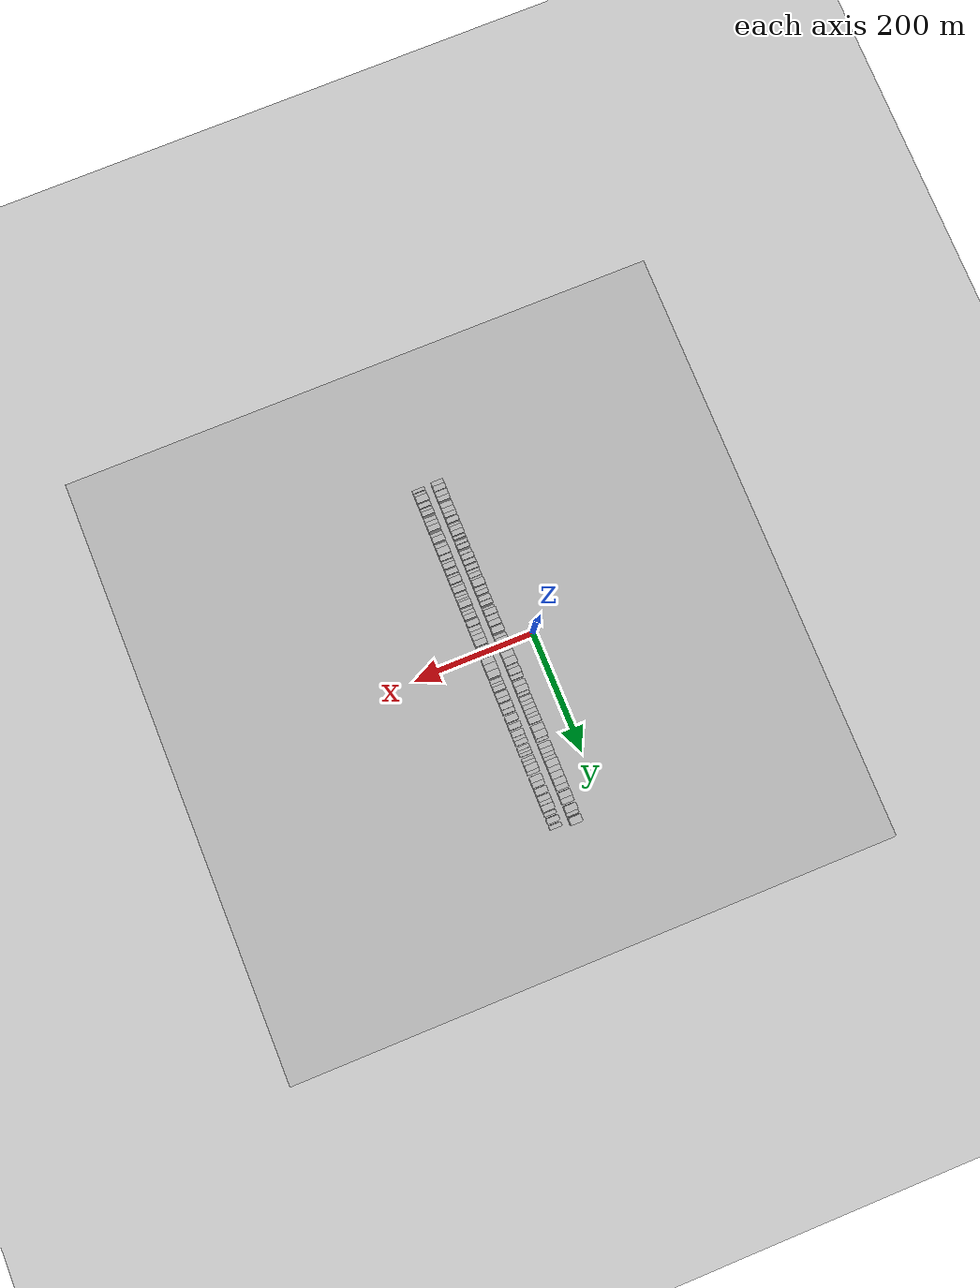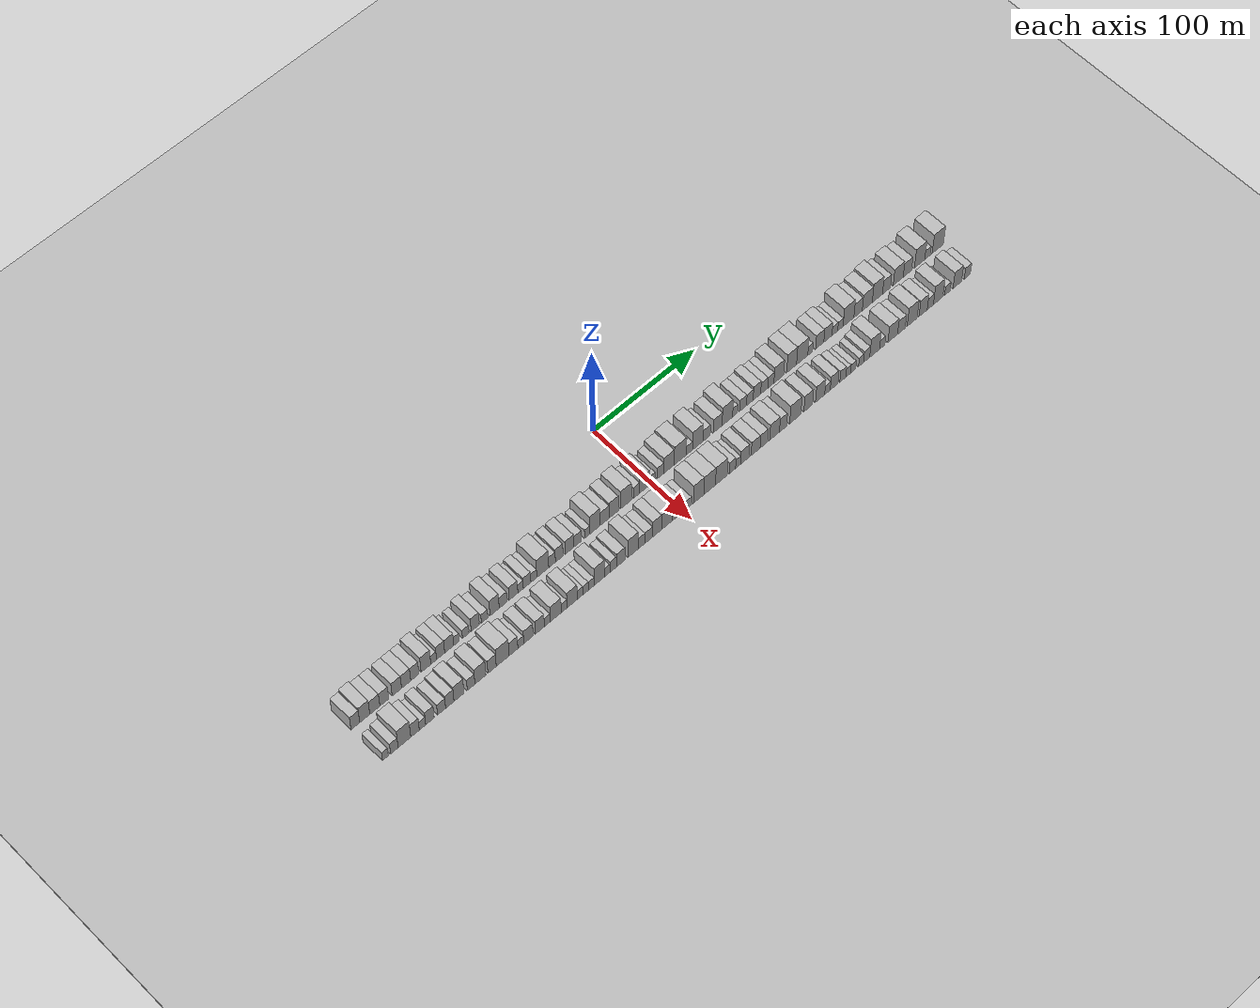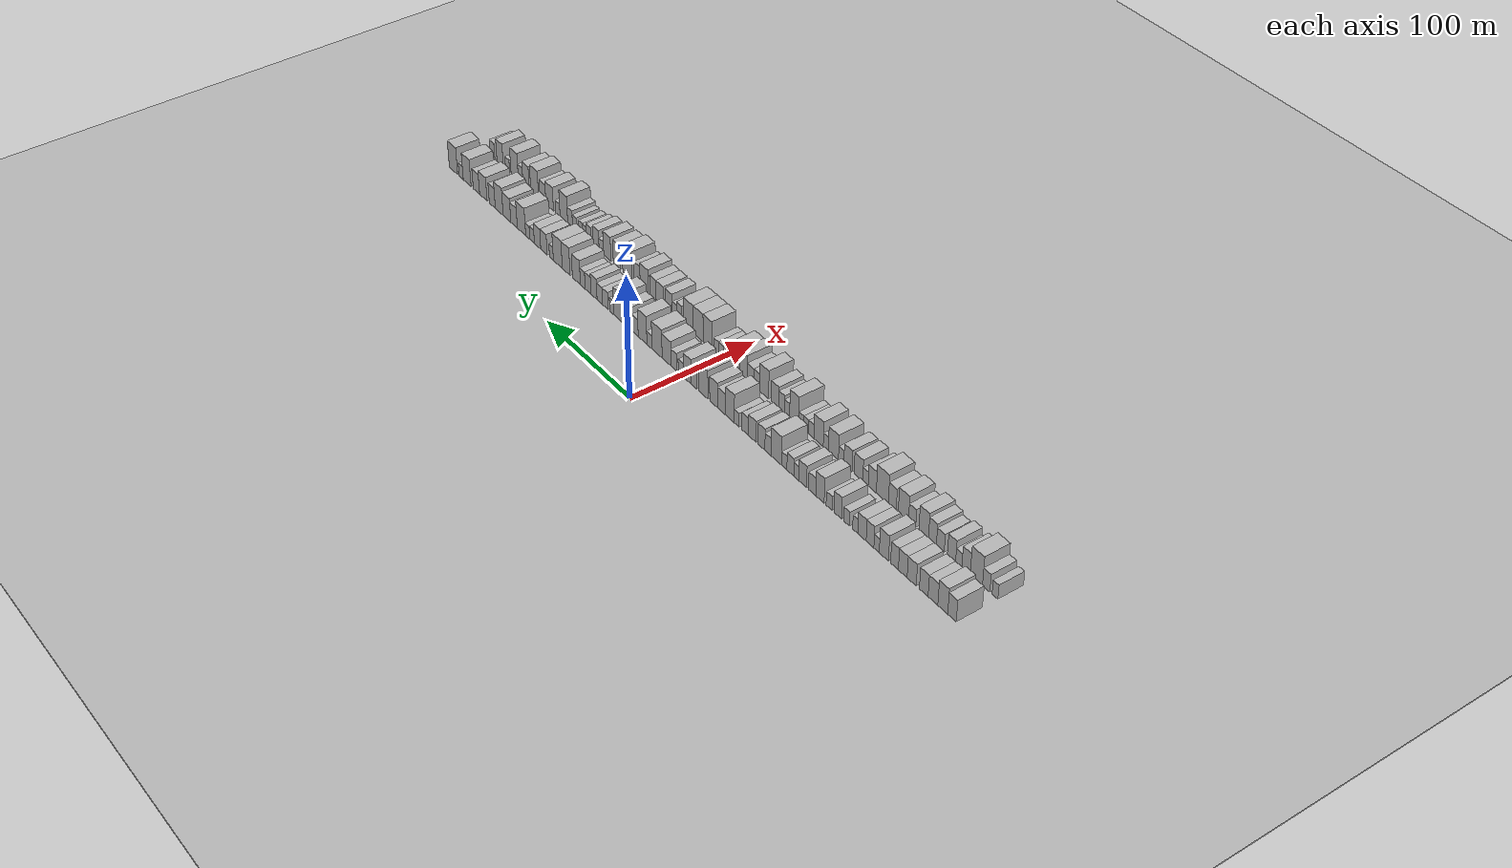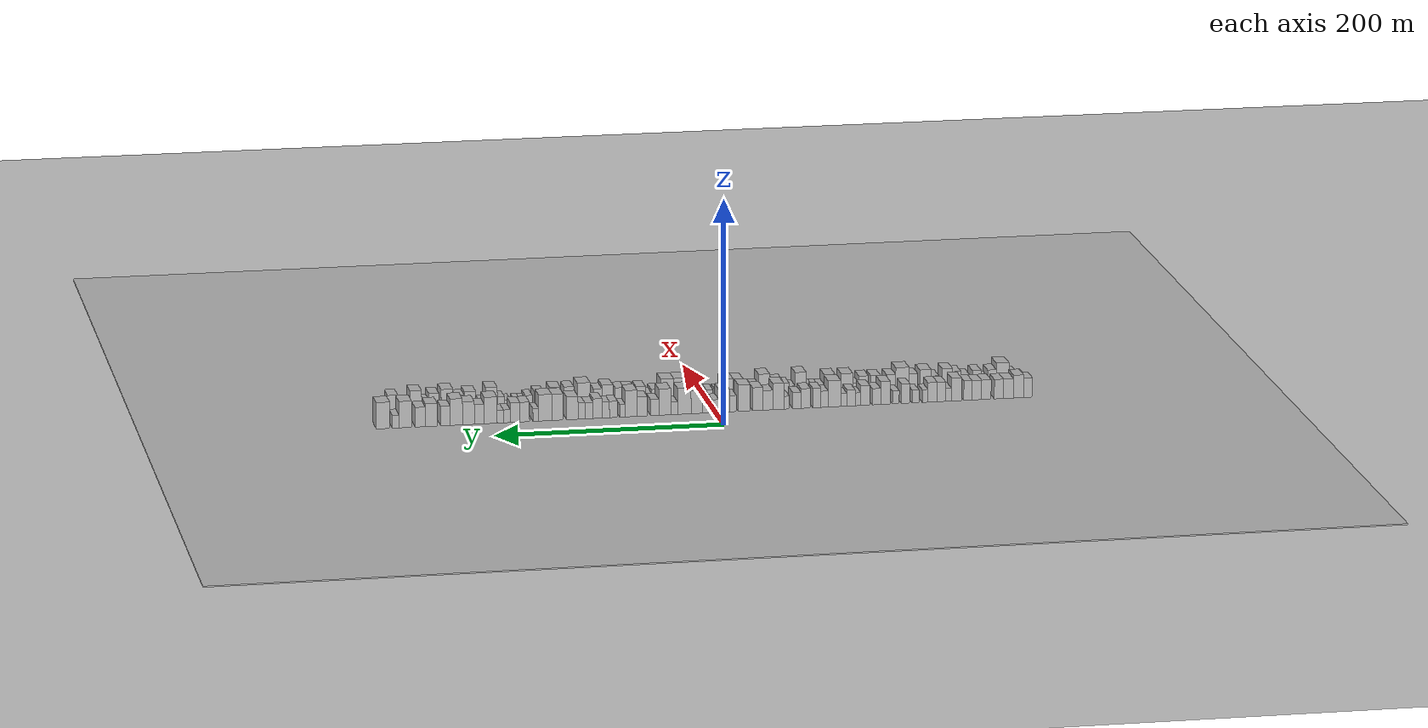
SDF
<?xml version="1.0" encoding="utf-8"?>

<sdf version="1.6">

   <world name="default">

      <gui fullscreen="0">

         <camera name="user_camera">

            <pose>-15 0 4.57585 0 0 0</pose>

            <view_controller>orbit</view_controller>

         </camera>

      </gui>

      <scene>

         <sky>

           <clouds>

             <speed>12</speed>

           </clouds>

         </sky>

         <ambient>0.4 0.4 0.4 1</ambient>

         <background>0.7 0.7 0.7 1</background>

         <shadows>1</shadows>

      </scene>

      <gravity>0 0 -9.8066</gravity>

      <magnetic_field>6e-06 2.3e-05 -4.2e-05</magnetic_field>

      <physics default="0" name="default_physics" type="ode">

         <ode>

            <solver>

               <type>quick</type>

               <iters>10</iters>

               <sor>1.0</sor>

               <use_dynamic_moi_rescaling>0</use_dynamic_moi_rescaling>

            </solver>

            <constraints>

               <cfm>0</cfm>

               <erp>0.2</erp>

               <contact_max_correcting_vel>100</contact_max_correcting_vel>

               <contact_surface_layer>0.001</contact_surface_layer>

            </constraints>

         </ode>

         <max_step_size>0.004</max_step_size>

         <real_time_factor>1</real_time_factor>

         <real_time_update_rate>250</real_time_update_rate>

      </physics>

      <light name="sun" type="directional">

         <cast_shadows>1</cast_shadows>

         <pose>0 0 10 0 0 0</pose>

         <diffuse>0.8 0.8 0.8 1</diffuse>

         <specular>0.2 0.2 0.2 1</specular>

         <attenuation>

            <range>1000</range>

            <constant>0.9</constant>

            <linear>0.01</linear>

            <quadratic>0.001</quadratic>

         </attenuation>

         <direction>-0.5 0.1 -0.9</direction>

      </light>

      <include>

         <name>ground_plane_1</name>

         <uri>model://HANNAS_ground_plane</uri>

         <pose>0 0 0  0 0 0</pose>

      </include>

      <include>

         <name>ground_plane_2</name>

         <uri>model://HANNAS_ground_plane</uri>

         <pose>100 0 0  0 0 0</pose>

      </include>

      <model name="building_1">

         <static>1</static>

         <pose frame="">50.0000 -277.0836 0 0.000000 0.000000 0.000000</pose>

         <link name="link">

            <pose frame="">0 0 9.00 0 0 0</pose>

            <collision name="collision">

               <geometry>

                  <box>

                     <size>20.0000 7.8328 18.0000</size>

                  </box>

               </geometry>

               <max_contacts>10</max_contacts>

               <surface>

                  <contact>

                     <ode/>

                  </contact>

                  <bounce/>

                  <friction>

                     <torsional>

                        <ode/>

                     </torsional>

                     <ode/>

                  </friction>

               </surface>

            </collision>

            <visual name="visual">

               <cast_shadows>0</cast_shadows>

               <geometry>

                  <box>

                     <size>20.0000 7.8328 18.0000</size>

                  </box>

               </geometry>

               <material>

                  <script>

                     <uri>model://HANNAS_wall/materials/scripts</uri>

                     <uri>model://HANNAS_wall/materials/textures</uri>

                     <name>vrc/HANNAS_wall</name>

                  </script>

               </material>

            </visual>

            <self_collide>0</self_collide>

            <enable_wind>0</enable_wind>

            <kinematic>0</kinematic>

         </link>

      </model>

      <model name="building_2">

         <static>1</static>

         <pose frame="">50.0000 -268.6406 0 0.000000 0.000000 0.000000</pose>

         <link name="link">

            <pose frame="">0 0 10.50 0 0 0</pose>

            <collision name="collision">

               <geometry>

                  <box>

                     <size>20.0000 9.0533 21.0000</size>

                  </box>

               </geometry>

               <max_contacts>10</max_contacts>

               <surface>

                  <contact>

                     <ode/>

                  </contact>

                  <bounce/>

                  <friction>

                     <torsional>

                        <ode/>

                     </torsional>

                     <ode/>

                  </friction>

               </surface>

            </collision>

            <visual name="visual">

               <cast_shadows>0</cast_shadows>

               <geometry>

                  <box>

                     <size>20.0000 9.0533 21.0000</size>

                  </box>

               </geometry>

               <material>

                  <script>

                     <uri>model://HANNAS_wall/materials/scripts</uri>

                     <uri>model://HANNAS_wall/materials/textures</uri>

                     <name>vrc/HANNAS_wall</name>

                  </script>

               </material>

            </visual>

            <self_collide>0</self_collide>

            <enable_wind>0</enable_wind>

            <kinematic>0</kinematic>

         </link>

      </model>

      <model name="building_3">

         <static>1</static>

         <pose frame="">50.0000 -259.6193 0 0.000000 0.000000 0.000000</pose>

         <link name="link">

            <pose frame="">0 0 9.00 0 0 0</pose>

            <collision name="collision">

               <geometry>

                  <box>

                     <size>20.0000 8.9893 18.0000</size>

                  </box>

               </geometry>

               <max_contacts>10</max_contacts>

               <surface>

                  <contact>

                     <ode/>

                  </contact>

                  <bounce/>

                  <friction>

                     <torsional>

                        <ode/>

                     </torsional>

                     <ode/>

                  </friction>

               </surface>

            </collision>

            <visual name="visual">

               <cast_shadows>0</cast_shadows>

               <geometry>

                  <box>

                     <size>20.0000 8.9893 18.0000</size>

                  </box>

               </geometry>

               <material>

                  <script>

                     <uri>model://HANNAS_wall/materials/scripts</uri>

                     <uri>model://HANNAS_wall/materials/textures</uri>

                     <name>vrc/HANNAS_wall</name>

                  </script>

               </material>

            </visual>

            <self_collide>0</self_collide>

            <enable_wind>0</enable_wind>

            <kinematic>0</kinematic>

         </link>

      </model>

      <model name="building_4">

         <static>1</static>

         <pose frame="">50.0000 -251.0663 0 0.000000 0.000000 0.000000</pose>

         <link name="link">

            <pose frame="">0 0 9.00 0 0 0</pose>

            <collision name="collision">

               <geometry>

                  <box>

                     <size>20.0000 8.1167 18.0000</size>

                  </box>

               </geometry>

               <max_contacts>10</max_contacts>

               <surface>

                  <contact>

                     <ode/>

                  </contact>

                  <bounce/>

                  <friction>

                     <torsional>

                        <ode/>

                     </torsional>

                     <ode/>

                  </friction>

               </surface>

            </collision>

            <visual name="visual">

               <cast_shadows>0</cast_shadows>

               <geometry>

                  <box>

                     <size>20.0000 8.1167 18.0000</size>

                  </box>

               </geometry>

               <material>

                  <script>

                     <uri>model://HANNAS_wall/materials/scripts</uri>

                     <uri>model://HANNAS_wall/materials/textures</uri>

                     <name>vrc/HANNAS_wall</name>

                  </script>

               </material>

            </visual>

            <self_collide>0</self_collide>

            <enable_wind>0</enable_wind>

            <kinematic>0</kinematic>

         </link>

      </model>

      <model name="building_5">

         <static>1</static>

         <pose frame="">50.0000 -239.7565 0 0.000000 0.000000 0.000000</pose>

         <link name="link">

            <pose frame="">0 0 9.00 0 0 0</pose>

            <collision name="collision">

               <geometry>

                  <box>

                     <size>20.0000 8.5028 18.0000</size>

                  </box>

               </geometry>

               <max_contacts>10</max_contacts>

               <surface>

                  <contact>

                     <ode/>

                  </contact>

                  <bounce/>

                  <friction>

                     <torsional>

                        <ode/>

                     </torsional>

                     <ode/>

                  </friction>

               </surface>

            </collision>

            <visual name="visual">

               <cast_shadows>0</cast_shadows>

               <geometry>

                  <box>

                     <size>20.0000 8.5028 18.0000</size>

                  </box>

               </geometry>

               <material>

                  <script>

                     <uri>model://HANNAS_wall/materials/scripts</uri>

                     <uri>model://HANNAS_wall/materials/textures</uri>

                     <name>vrc/HANNAS_wall</name>

                  </script>

               </material>

            </visual>

            <self_collide>0</self_collide>

            <enable_wind>0</enable_wind>

            <kinematic>0</kinematic>

         </link>

      </model>

      <model name="building_6">

         <static>1</static>

         <pose frame="">50.0000 -231.3192 0 0.000000 0.000000 0.000000</pose>

         <link name="link">

            <pose frame="">0 0 9.00 0 0 0</pose>

            <collision name="collision">

               <geometry>

                  <box>

                     <size>20.0000 8.3718 18.0000</size>

                  </box>

               </geometry>

               <max_contacts>10</max_contacts>

               <surface>

                  <contact>

                     <ode/>

                  </contact>

                  <bounce/>

                  <friction>

                     <torsional>

                        <ode/>

                     </torsional>

                     <ode/>

                  </friction>

               </surface>

            </collision>

            <visual name="visual">

               <cast_shadows>0</cast_shadows>

               <geometry>

                  <box>

                     <size>20.0000 8.3718 18.0000</size>

                  </box>

               </geometry>

               <material>

                  <script>

                     <uri>model://HANNAS_wall/materials/scripts</uri>

                     <uri>model://HANNAS_wall/materials/textures</uri>

                     <name>vrc/HANNAS_wall</name>

                  </script>

               </material>

            </visual>

            <self_collide>0</self_collide>

            <enable_wind>0</enable_wind>

            <kinematic>0</kinematic>

         </link>

      </model>

      <model name="building_7">

         <static>1</static>

         <pose frame="">50.0000 -223.4350 0 0.000000 0.000000 0.000000</pose>

         <link name="link">

            <pose frame="">0 0 9.00 0 0 0</pose>

            <collision name="collision">

               <geometry>

                  <box>

                     <size>20.0000 7.3966 18.0000</size>

                  </box>

               </geometry>

               <max_contacts>10</max_contacts>

               <surface>

                  <contact>

                     <ode/>

                  </contact>

                  <bounce/>

                  <friction>

                     <torsional>

                        <ode/>

                     </torsional>

                     <ode/>

                  </friction>

               </surface>

            </collision>

            <visual name="visual">

               <cast_shadows>0</cast_shadows>

               <geometry>

                  <box>

                     <size>20.0000 7.3966 18.0000</size>

                  </box>

               </geometry>

               <material>

                  <script>

                     <uri>model://HANNAS_wall/materials/scripts</uri>

                     <uri>model://HANNAS_wall/materials/textures</uri>

                     <name>vrc/HANNAS_wall</name>

                  </script>

               </material>

            </visual>

            <self_collide>0</self_collide>

            <enable_wind>0</enable_wind>

            <kinematic>0</kinematic>

         </link>

      </model>

      <model name="building_8">

         <static>1</static>

         <pose frame="">50.0000 -213.2876 0 0.000000 0.000000 0.000000</pose>

         <link name="link">

            <pose frame="">0 0 10.50 0 0 0</pose>

            <collision name="collision">

               <geometry>

                  <box>

                     <size>20.0000 8.8982 21.0000</size>

                  </box>

               </geometry>

               <max_contacts>10</max_contacts>

               <surface>

                  <contact>

                     <ode/>

                  </contact>

                  <bounce/>

                  <friction>

                     <torsional>

                        <ode/>

                     </torsional>

                     <ode/>

                  </friction>

               </surface>

            </collision>

            <visual name="visual">

               <cast_shadows>0</cast_shadows>

               <geometry>

                  <box>

                     <size>20.0000 8.8982 21.0000</size>

                  </box>

               </geometry>

               <material>

                  <script>

                     <uri>model://HANNAS_wall/materials/scripts</uri>

                     <uri>model://HANNAS_wall/materials/textures</uri>

                     <name>vrc/HANNAS_wall</name>

                  </script>

               </material>

            </visual>

            <self_collide>0</self_collide>

            <enable_wind>0</enable_wind>

            <kinematic>0</kinematic>

         </link>

      </model>

      <model name="building_9">

         <static>1</static>

         <pose frame="">50.0000 -206.2193 0 0.000000 0.000000 0.000000</pose>

         <link name="link">

            <pose frame="">0 0 6.00 0 0 0</pose>

            <collision name="collision">

               <geometry>

                  <box>

                     <size>20.0000 5.2385 12.0000</size>

                  </box>

               </geometry>

               <max_contacts>10</max_contacts>

               <surface>

                  <contact>

                     <ode/>

                  </contact>

                  <bounce/>

                  <friction>

                     <torsional>

                        <ode/>

                     </torsional>

                     <ode/>

                  </friction>

               </surface>

            </collision>

            <visual name="visual">

               <cast_shadows>0</cast_shadows>

               <geometry>

                  <box>

                     <size>20.0000 5.2385 12.0000</size>

                  </box>

               </geometry>

               <material>

                  <script>

                     <uri>model://HANNAS_wall/materials/scripts</uri>

                     <uri>model://HANNAS_wall/materials/textures</uri>

                     <name>vrc/HANNAS_wall</name>

                  </script>

               </material>

            </visual>

            <self_collide>0</self_collide>

            <enable_wind>0</enable_wind>

            <kinematic>0</kinematic>

         </link>

      </model>

      <model name="building_10">

         <static>1</static>

         <pose frame="">50.0000 -199.8635 0 0.000000 0.000000 0.000000</pose>

         <link name="link">

            <pose frame="">0 0 9.00 0 0 0</pose>

            <collision name="collision">

               <geometry>

                  <box>

                     <size>20.0000 7.4730 18.0000</size>

                  </box>

               </geometry>

               <max_contacts>10</max_contacts>

               <surface>

                  <contact>

                     <ode/>

                  </contact>

                  <bounce/>

                  <friction>

                     <torsional>

                        <ode/>

                     </torsional>

                     <ode/>

                  </friction>

               </surface>

            </collision>

            <visual name="visual">

               <cast_shadows>0</cast_shadows>

               <geometry>

                  <box>

                     <size>20.0000 7.4730 18.0000</size>

                  </box>

               </geometry>

               <material>

                  <script>

                     <uri>model://HANNAS_wall/materials/scripts</uri>

                     <uri>model://HANNAS_wall/materials/textures</uri>

                     <name>vrc/HANNAS_wall</name>

                  </script>

               </material>

            </visual>

            <self_collide>0</self_collide>

            <enable_wind>0</enable_wind>

            <kinematic>0</kinematic>

         </link>

      </model>

      <model name="building_11">

         <static>1</static>

         <pose frame="">50.0000 -191.9743 0 0.000000 0.000000 0.000000</pose>

         <link name="link">

            <pose frame="">0 0 9.00 0 0 0</pose>

            <collision name="collision">

               <geometry>

                  <box>

                     <size>20.0000 8.3054 18.0000</size>

                  </box>

               </geometry>

               <max_contacts>10</max_contacts>

               <surface>

                  <contact>

                     <ode/>

                  </contact>

                  <bounce/>

                  <friction>

                     <torsional>

                        <ode/>

                     </torsional>

                     <ode/>

                  </friction>

               </surface>

            </collision>

            <visual name="visual">

               <cast_shadows>0</cast_shadows>

               <geometry>

                  <box>

                     <size>20.0000 8.3054 18.0000</size>

                  </box>

               </geometry>

               <material>

                  <script>

                     <uri>model://HANNAS_wall/materials/scripts</uri>

                     <uri>model://HANNAS_wall/materials/textures</uri>

                     <name>vrc/HANNAS_wall</name>

                  </script>

               </material>

            </visual>

            <self_collide>0</self_collide>

            <enable_wind>0</enable_wind>

            <kinematic>0</kinematic>

         </link>

      </model>

      <model name="building_12">

         <static>1</static>

         <pose frame="">50.0000 -185.3072 0 0.000000 0.000000 0.000000</pose>

         <link name="link">

            <pose frame="">0 0 6.00 0 0 0</pose>

            <collision name="collision">

               <geometry>

                  <box>

                     <size>20.0000 5.0287 12.0000</size>

                  </box>

               </geometry>

               <max_contacts>10</max_contacts>

               <surface>

                  <contact>

                     <ode/>

                  </contact>

                  <bounce/>

                  <friction>

                     <torsional>

                        <ode/>

                     </torsional>

                     <ode/>

                  </friction>

               </surface>

            </collision>

            <visual name="visual">

               <cast_shadows>0</cast_shadows>

               <geometry>

                  <box>

                     <size>20.0000 5.0287 12.0000</size>

                  </box>

               </geometry>

               <material>

                  <script>

                     <uri>model://HANNAS_wall/materials/scripts</uri>

                     <uri>model://HANNAS_wall/materials/textures</uri>

                     <name>vrc/HANNAS_wall</name>

                  </script>

               </material>

            </visual>

            <self_collide>0</self_collide>

            <enable_wind>0</enable_wind>

            <kinematic>0</kinematic>

         </link>

      </model>

      <model name="building_13">

         <static>1</static>

         <pose frame="">50.0000 -176.8049 0 0.000000 0.000000 0.000000</pose>

         <link name="link">

            <pose frame="">0 0 6.00 0 0 0</pose>

            <collision name="collision">

               <geometry>

                  <box>

                     <size>20.0000 5.9760 12.0000</size>

                  </box>

               </geometry>

               <max_contacts>10</max_contacts>

               <surface>

                  <contact>

                     <ode/>

                  </contact>

                  <bounce/>

                  <friction>

                     <torsional>

                        <ode/>

                     </torsional>

                     <ode/>

                  </friction>

               </surface>

            </collision>

            <visual name="visual">

               <cast_shadows>0</cast_shadows>

               <geometry>

                  <box>

                     <size>20.0000 5.9760 12.0000</size>

                  </box>

               </geometry>

               <material>

                  <script>

                     <uri>model://HANNAS_wall/materials/scripts</uri>

                     <uri>model://HANNAS_wall/materials/textures</uri>

                     <name>vrc/HANNAS_wall</name>

                  </script>

               </material>

            </visual>

            <self_collide>0</self_collide>

            <enable_wind>0</enable_wind>

            <kinematic>0</kinematic>

         </link>

      </model>

      <model name="building_14">

         <static>1</static>

         <pose frame="">50.0000 -168.0518 0 0.000000 0.000000 0.000000</pose>

         <link name="link">

            <pose frame="">0 0 9.00 0 0 0</pose>

            <collision name="collision">

               <geometry>

                  <box>

                     <size>20.0000 7.5302 18.0000</size>

                  </box>

               </geometry>

               <max_contacts>10</max_contacts>

               <surface>

                  <contact>

                     <ode/>

                  </contact>

                  <bounce/>

                  <friction>

                     <torsional>

                        <ode/>

                     </torsional>

                     <ode/>

                  </friction>

               </surface>

            </collision>

            <visual name="visual">

               <cast_shadows>0</cast_shadows>

               <geometry>

                  <box>

                     <size>20.0000 7.5302 18.0000</size>

                  </box>

               </geometry>

               <material>

                  <script>

                     <uri>model://HANNAS_wall/materials/scripts</uri>

                     <uri>model://HANNAS_wall/materials/textures</uri>

                     <name>vrc/HANNAS_wall</name>

                  </script>

               </material>

            </visual>

            <self_collide>0</self_collide>

            <enable_wind>0</enable_wind>

            <kinematic>0</kinematic>

         </link>

      </model>

      <model name="building_15">

         <static>1</static>

         <pose frame="">50.0000 -159.2871 0 0.000000 0.000000 0.000000</pose>

         <link name="link">

            <pose frame="">0 0 6.00 0 0 0</pose>

            <collision name="collision">

               <geometry>

                  <box>

                     <size>20.0000 5.9992 12.0000</size>

                  </box>

               </geometry>

               <max_contacts>10</max_contacts>

               <surface>

                  <contact>

                     <ode/>

                  </contact>

                  <bounce/>

                  <friction>

                     <torsional>

                        <ode/>

                     </torsional>

                     <ode/>

                  </friction>

               </surface>

            </collision>

            <visual name="visual">

               <cast_shadows>0</cast_shadows>

               <geometry>

                  <box>

                     <size>20.0000 5.9992 12.0000</size>

                  </box>

               </geometry>

               <material>

                  <script>

                     <uri>model://HANNAS_wall/materials/scripts</uri>

                     <uri>model://HANNAS_wall/materials/textures</uri>

                     <name>vrc/HANNAS_wall</name>

                  </script>

               </material>

            </visual>

            <self_collide>0</self_collide>

            <enable_wind>0</enable_wind>

            <kinematic>0</kinematic>

         </link>

      </model>

      <model name="building_16">

         <static>1</static>

         <pose frame="">50.0000 -150.0109 0 0.000000 0.000000 0.000000</pose>

         <link name="link">

            <pose frame="">0 0 10.50 0 0 0</pose>

            <collision name="collision">

               <geometry>

                  <box>

                     <size>20.0000 8.5532 21.0000</size>

                  </box>

               </geometry>

               <max_contacts>10</max_contacts>

               <surface>

                  <contact>

                     <ode/>

                  </contact>

                  <bounce/>

                  <friction>

                     <torsional>

                        <ode/>

                     </torsional>

                     <ode/>

                  </friction>

               </surface>

            </collision>

            <visual name="visual">

               <cast_shadows>0</cast_shadows>

               <geometry>

                  <box>

                     <size>20.0000 8.5532 21.0000</size>

                  </box>

               </geometry>

               <material>

                  <script>

                     <uri>model://HANNAS_wall/materials/scripts</uri>

                     <uri>model://HANNAS_wall/materials/textures</uri>

                     <name>vrc/HANNAS_wall</name>

                  </script>

               </material>

            </visual>

            <self_collide>0</self_collide>

            <enable_wind>0</enable_wind>

            <kinematic>0</kinematic>

         </link>

      </model>

      <model name="building_17">

         <static>1</static>

         <pose frame="">50.0000 -142.0953 0 0.000000 0.000000 0.000000</pose>

         <link name="link">

            <pose frame="">0 0 7.50 0 0 0</pose>

            <collision name="collision">

               <geometry>

                  <box>

                     <size>20.0000 7.2780 15.0000</size>

                  </box>

               </geometry>

               <max_contacts>10</max_contacts>

               <surface>

                  <contact>

                     <ode/>

                  </contact>

                  <bounce/>

                  <friction>

                     <torsional>

                        <ode/>

                     </torsional>

                     <ode/>

                  </friction>

               </surface>

            </collision>

            <visual name="visual">

               <cast_shadows>0</cast_shadows>

               <geometry>

                  <box>

                     <size>20.0000 7.2780 15.0000</size>

                  </box>

               </geometry>

               <material>

                  <script>

                     <uri>model://HANNAS_wall/materials/scripts</uri>

                     <uri>model://HANNAS_wall/materials/textures</uri>

                     <name>vrc/HANNAS_wall</name>

                  </script>

               </material>

            </visual>

            <self_collide>0</self_collide>

            <enable_wind>0</enable_wind>

            <kinematic>0</kinematic>

         </link>

      </model>

      <model name="building_18">

         <static>1</static>

         <pose frame="">50.0000 -132.3448 0 0.000000 0.000000 0.000000</pose>

         <link name="link">

            <pose frame="">0 0 9.00 0 0 0</pose>

            <collision name="collision">

               <geometry>

                  <box>

                     <size>20.0000 8.2228 18.0000</size>

                  </box>

               </geometry>

               <max_contacts>10</max_contacts>

               <surface>

                  <contact>

                     <ode/>

                  </contact>

                  <bounce/>

                  <friction>

                     <torsional>

                        <ode/>

                     </torsional>

                     <ode/>

                  </friction>

               </surface>

            </collision>

            <visual name="visual">

               <cast_shadows>0</cast_shadows>

               <geometry>

                  <box>

                     <size>20.0000 8.2228 18.0000</size>

                  </box>

               </geometry>

               <material>

                  <script>

                     <uri>model://HANNAS_wall/materials/scripts</uri>

                     <uri>model://HANNAS_wall/materials/textures</uri>

                     <name>vrc/HANNAS_wall</name>

                  </script>

               </material>

            </visual>

            <self_collide>0</self_collide>

            <enable_wind>0</enable_wind>

            <kinematic>0</kinematic>

         </link>

      </model>

      <model name="building_19">

         <static>1</static>

         <pose frame="">50.0000 -125.6786 0 0.000000 0.000000 0.000000</pose>

         <link name="link">

            <pose frame="">0 0 6.00 0 0 0</pose>

            <collision name="collision">

               <geometry>

                  <box>

                     <size>20.0000 5.1096 12.0000</size>

                  </box>

               </geometry>

               <max_contacts>10</max_contacts>

               <surface>

                  <contact>

                     <ode/>

                  </contact>

                  <bounce/>

                  <friction>

                     <torsional>

                        <ode/>

                     </torsional>

                     <ode/>

                  </friction>

               </surface>

            </collision>

            <visual name="visual">

               <cast_shadows>0</cast_shadows>

               <geometry>

                  <box>

                     <size>20.0000 5.1096 12.0000</size>

                  </box>

               </geometry>

               <material>

                  <script>

                     <uri>model://HANNAS_wall/materials/scripts</uri>

                     <uri>model://HANNAS_wall/materials/textures</uri>

                     <name>vrc/HANNAS_wall</name>

                  </script>

               </material>

            </visual>

            <self_collide>0</self_collide>

            <enable_wind>0</enable_wind>

            <kinematic>0</kinematic>

         </link>

      </model>

      <model name="building_20">

         <static>1</static>

         <pose frame="">50.0000 -119.5632 0 0.000000 0.000000 0.000000</pose>

         <link name="link">

            <pose frame="">0 0 7.50 0 0 0</pose>

            <collision name="collision">

               <geometry>

                  <box>

                     <size>20.0000 7.1214 15.0000</size>

                  </box>

               </geometry>

               <max_contacts>10</max_contacts>

               <surface>

                  <contact>

                     <ode/>

                  </contact>

                  <bounce/>

                  <friction>

                     <torsional>

                        <ode/>

                     </torsional>

                     <ode/>

                  </friction>

               </surface>

            </collision>

            <visual name="visual">

               <cast_shadows>0</cast_shadows>

               <geometry>

                  <box>

                     <size>20.0000 7.1214 15.0000</size>

                  </box>

               </geometry>

               <material>

                  <script>

                     <uri>model://HANNAS_wall/materials/scripts</uri>

                     <uri>model://HANNAS_wall/materials/textures</uri>

                     <name>vrc/HANNAS_wall</name>

                  </script>

               </material>

            </visual>

            <self_collide>0</self_collide>

            <enable_wind>0</enable_wind>

            <kinematic>0</kinematic>

         </link>

      </model>

      <model name="building_21">

         <static>1</static>

         <pose frame="">50.0000 -113.2214 0 0.000000 0.000000 0.000000</pose>

         <link name="link">

            <pose frame="">0 0 6.00 0 0 0</pose>

            <collision name="collision">

               <geometry>

                  <box>

                     <size>20.0000 5.5622 12.0000</size>

                  </box>

               </geometry>

               <max_contacts>10</max_contacts>

               <surface>

                  <contact>

                     <ode/>

                  </contact>

                  <bounce/>

                  <friction>

                     <torsional>

                        <ode/>

                     </torsional>

                     <ode/>

                  </friction>

               </surface>

            </collision>

            <visual name="visual">

               <cast_shadows>0</cast_shadows>

               <geometry>

                  <box>

                     <size>20.0000 5.5622 12.0000</size>

                  </box>

               </geometry>

               <material>

                  <script>

                     <uri>model://HANNAS_wall/materials/scripts</uri>

                     <uri>model://HANNAS_wall/materials/textures</uri>

                     <name>vrc/HANNAS_wall</name>

                  </script>

               </material>

            </visual>

            <self_collide>0</self_collide>

            <enable_wind>0</enable_wind>

            <kinematic>0</kinematic>

         </link>

      </model>

      <model name="building_22">

         <static>1</static>

         <pose frame="">50.0000 -104.7988 0 0.000000 0.000000 0.000000</pose>

         <link name="link">

            <pose frame="">0 0 12.00 0 0 0</pose>

            <collision name="collision">

               <geometry>

                  <box>

                     <size>20.0000 11.2829 24.0000</size>

                  </box>

               </geometry>

               <max_contacts>10</max_contacts>

               <surface>

                  <contact>

                     <ode/>

                  </contact>

                  <bounce/>

                  <friction>

                     <torsional>

                        <ode/>

                     </torsional>

                     <ode/>

                  </friction>

               </surface>

            </collision>

            <visual name="visual">

               <cast_shadows>0</cast_shadows>

               <geometry>

                  <box>

                     <size>20.0000 11.2829 24.0000</size>

                  </box>

               </geometry>

               <material>

                  <script>

                     <uri>model://HANNAS_wall/materials/scripts</uri>

                     <uri>model://HANNAS_wall/materials/textures</uri>

                     <name>vrc/HANNAS_wall</name>

                  </script>

               </material>

            </visual>

            <self_collide>0</self_collide>

            <enable_wind>0</enable_wind>

            <kinematic>0</kinematic>

         </link>

      </model>

      <model name="building_23">

         <static>1</static>

         <pose frame="">50.0000 -95.9924 0 0.000000 0.000000 0.000000</pose>

         <link name="link">

            <pose frame="">0 0 7.50 0 0 0</pose>

            <collision name="collision">

               <geometry>

                  <box>

                     <size>20.0000 6.3301 15.0000</size>

                  </box>

               </geometry>

               <max_contacts>10</max_contacts>

               <surface>

                  <contact>

                     <ode/>

                  </contact>

                  <bounce/>

                  <friction>

                     <torsional>

                        <ode/>

                     </torsional>

                     <ode/>

                  </friction>

               </surface>

            </collision>

            <visual name="visual">

               <cast_shadows>0</cast_shadows>

               <geometry>

                  <box>

                     <size>20.0000 6.3301 15.0000</size>

                  </box>

               </geometry>

               <material>

                  <script>

                     <uri>model://HANNAS_wall/materials/scripts</uri>

                     <uri>model://HANNAS_wall/materials/textures</uri>

                     <name>vrc/HANNAS_wall</name>

                  </script>

               </material>

            </visual>

            <self_collide>0</self_collide>

            <enable_wind>0</enable_wind>

            <kinematic>0</kinematic>

         </link>

      </model>

      <model name="building_24">

         <static>1</static>

         <pose frame="">50.0000 -89.2120 0 0.000000 0.000000 0.000000</pose>

         <link name="link">

            <pose frame="">0 0 9.00 0 0 0</pose>

            <collision name="collision">

               <geometry>

                  <box>

                     <size>20.0000 7.2307 18.0000</size>

                  </box>

               </geometry>

               <max_contacts>10</max_contacts>

               <surface>

                  <contact>

                     <ode/>

                  </contact>

                  <bounce/>

                  <friction>

                     <torsional>

                        <ode/>

                     </torsional>

                     <ode/>

                  </friction>

               </surface>

            </collision>

            <visual name="visual">

               <cast_shadows>0</cast_shadows>

               <geometry>

                  <box>

                     <size>20.0000 7.2307 18.0000</size>

                  </box>

               </geometry>

               <material>

                  <script>

                     <uri>model://HANNAS_wall/materials/scripts</uri>

                     <uri>model://HANNAS_wall/materials/textures</uri>

                     <name>vrc/HANNAS_wall</name>

                  </script>

               </material>

            </visual>

            <self_collide>0</self_collide>

            <enable_wind>0</enable_wind>

            <kinematic>0</kinematic>

         </link>

      </model>

      <model name="building_25">

         <static>1</static>

         <pose frame="">50.0000 -79.4001 0 0.000000 0.000000 0.000000</pose>

         <link name="link">

            <pose frame="">0 0 9.00 0 0 0</pose>

            <collision name="collision">

               <geometry>

                  <box>

                     <size>20.0000 8.3930 18.0000</size>

                  </box>

               </geometry>

               <max_contacts>10</max_contacts>

               <surface>

                  <contact>

                     <ode/>

                  </contact>

                  <bounce/>

                  <friction>

                     <torsional>

                        <ode/>

                     </torsional>

                     <ode/>

                  </friction>

               </surface>

            </collision>

            <visual name="visual">

               <cast_shadows>0</cast_shadows>

               <geometry>

                  <box>

                     <size>20.0000 8.3930 18.0000</size>

                  </box>

               </geometry>

               <material>

                  <script>

                     <uri>model://HANNAS_wall/materials/scripts</uri>

                     <uri>model://HANNAS_wall/materials/textures</uri>

                     <name>vrc/HANNAS_wall</name>

                  </script>

               </material>

            </visual>

            <self_collide>0</self_collide>

            <enable_wind>0</enable_wind>

            <kinematic>0</kinematic>

         </link>

      </model>

      <model name="building_26">

         <static>1</static>

         <pose frame="">50.0000 -71.6414 0 0.000000 0.000000 0.000000</pose>

         <link name="link">

            <pose frame="">0 0 7.50 0 0 0</pose>

            <collision name="collision">

               <geometry>

                  <box>

                     <size>20.0000 7.1246 15.0000</size>

                  </box>

               </geometry>

               <max_contacts>10</max_contacts>

               <surface>

                  <contact>

                     <ode/>

                  </contact>

                  <bounce/>

                  <friction>

                     <torsional>

                        <ode/>

                     </torsional>

                     <ode/>

                  </friction>

               </surface>

            </collision>

            <visual name="visual">

               <cast_shadows>0</cast_shadows>

               <geometry>

                  <box>

                     <size>20.0000 7.1246 15.0000</size>

                  </box>

               </geometry>

               <material>

                  <script>

                     <uri>model://HANNAS_wall/materials/scripts</uri>

                     <uri>model://HANNAS_wall/materials/textures</uri>

                     <name>vrc/HANNAS_wall</name>

                  </script>

               </material>

            </visual>

            <self_collide>0</self_collide>

            <enable_wind>0</enable_wind>

            <kinematic>0</kinematic>

         </link>

      </model>

      <model name="building_27">

         <static>1</static>

         <pose frame="">50.0000 -62.5019 0 0.000000 0.000000 0.000000</pose>

         <link name="link">

            <pose frame="">0 0 6.00 0 0 0</pose>

            <collision name="collision">

               <geometry>

                  <box>

                     <size>20.0000 5.1543 12.0000</size>

                  </box>

               </geometry>

               <max_contacts>10</max_contacts>

               <surface>

                  <contact>

                     <ode/>

                  </contact>

                  <bounce/>

                  <friction>

                     <torsional>

                        <ode/>

                     </torsional>

                     <ode/>

                  </friction>

               </surface>

            </collision>

            <visual name="visual">

               <cast_shadows>0</cast_shadows>

               <geometry>

                  <box>

                     <size>20.0000 5.1543 12.0000</size>

                  </box>

               </geometry>

               <material>

                  <script>

                     <uri>model://HANNAS_wall/materials/scripts</uri>

                     <uri>model://HANNAS_wall/materials/textures</uri>

                     <name>vrc/HANNAS_wall</name>

                  </script>

               </material>

            </visual>

            <self_collide>0</self_collide>

            <enable_wind>0</enable_wind>

            <kinematic>0</kinematic>

         </link>

      </model>

      <model name="building_28">

         <static>1</static>

         <pose frame="">50.0000 -55.0729 0 0.000000 0.000000 0.000000</pose>

         <link name="link">

            <pose frame="">0 0 12.00 0 0 0</pose>

            <collision name="collision">

               <geometry>

                  <box>

                     <size>20.0000 9.7038 24.0000</size>

                  </box>

               </geometry>

               <max_contacts>10</max_contacts>

               <surface>

                  <contact>

                     <ode/>

                  </contact>

                  <bounce/>

                  <friction>

                     <torsional>

                        <ode/>

                     </torsional>

                     <ode/>

                  </friction>

               </surface>

            </collision>

            <visual name="visual">

               <cast_shadows>0</cast_shadows>

               <geometry>

                  <box>

                     <size>20.0000 9.7038 24.0000</size>

                  </box>

               </geometry>

               <material>

                  <script>

                     <uri>model://HANNAS_wall/materials/scripts</uri>

                     <uri>model://HANNAS_wall/materials/textures</uri>

                     <name>vrc/HANNAS_wall</name>

                  </script>

               </material>

            </visual>

            <self_collide>0</self_collide>

            <enable_wind>0</enable_wind>

            <kinematic>0</kinematic>

         </link>

      </model>

      <model name="building_29">

         <static>1</static>

         <pose frame="">50.0000 -45.8381 0 0.000000 0.000000 0.000000</pose>

         <link name="link">

            <pose frame="">0 0 9.00 0 0 0</pose>

            <collision name="collision">

               <geometry>

                  <box>

                     <size>20.0000 8.7659 18.0000</size>

                  </box>

               </geometry>

               <max_contacts>10</max_contacts>

               <surface>

                  <contact>

                     <ode/>

                  </contact>

                  <bounce/>

                  <friction>

                     <torsional>

                        <ode/>

                     </torsional>

                     <ode/>

                  </friction>

               </surface>

            </collision>

            <visual name="visual">

               <cast_shadows>0</cast_shadows>

               <geometry>

                  <box>

                     <size>20.0000 8.7659 18.0000</size>

                  </box>

               </geometry>

               <material>

                  <script>

                     <uri>model://HANNAS_wall/materials/scripts</uri>

                     <uri>model://HANNAS_wall/materials/textures</uri>

                     <name>vrc/HANNAS_wall</name>

                  </script>

               </material>

            </visual>

            <self_collide>0</self_collide>

            <enable_wind>0</enable_wind>

            <kinematic>0</kinematic>

         </link>

      </model>

      <model name="building_30">

         <static>1</static>

         <pose frame="">50.0000 -36.9854 0 0.000000 0.000000 0.000000</pose>

         <link name="link">

            <pose frame="">0 0 10.50 0 0 0</pose>

            <collision name="collision">

               <geometry>

                  <box>

                     <size>20.0000 8.9395 21.0000</size>

                  </box>

               </geometry>

               <max_contacts>10</max_contacts>

               <surface>

                  <contact>

                     <ode/>

                  </contact>

                  <bounce/>

                  <friction>

                     <torsional>

                        <ode/>

                     </torsional>

                     <ode/>

                  </friction>

               </surface>

            </collision>

            <visual name="visual">

               <cast_shadows>0</cast_shadows>

               <geometry>

                  <box>

                     <size>20.0000 8.9395 21.0000</size>

                  </box>

               </geometry>

               <material>

                  <script>

                     <uri>model://HANNAS_wall/materials/scripts</uri>

                     <uri>model://HANNAS_wall/materials/textures</uri>

                     <name>vrc/HANNAS_wall</name>

                  </script>

               </material>

            </visual>

            <self_collide>0</self_collide>

            <enable_wind>0</enable_wind>

            <kinematic>0</kinematic>

         </link>

      </model>

      <model name="building_31">

         <static>1</static>

         <pose frame="">50.0000 -25.2559 0 0.000000 0.000000 0.000000</pose>

         <link name="link">

            <pose frame="">0 0 12.00 0 0 0</pose>

            <collision name="collision">

               <geometry>

                  <box>

                     <size>20.0000 10.5196 24.0000</size>

                  </box>

               </geometry>

               <max_contacts>10</max_contacts>

               <surface>

                  <contact>

                     <ode/>

                  </contact>

                  <bounce/>

                  <friction>

                     <torsional>

                        <ode/>

                     </torsional>

                     <ode/>

                  </friction>

               </surface>

            </collision>

            <visual name="visual">

               <cast_shadows>0</cast_shadows>

               <geometry>

                  <box>

                     <size>20.0000 10.5196 24.0000</size>

                  </box>

               </geometry>

               <material>

                  <script>

                     <uri>model://HANNAS_wall/materials/scripts</uri>

                     <uri>model://HANNAS_wall/materials/textures</uri>

                     <name>vrc/HANNAS_wall</name>

                  </script>

               </material>

            </visual>

            <self_collide>0</self_collide>

            <enable_wind>0</enable_wind>

            <kinematic>0</kinematic>

         </link>

      </model>

      <model name="building_32">

         <static>1</static>

         <pose frame="">50.0000 -14.9282 0 0.000000 0.000000 0.000000</pose>

         <link name="link">

            <pose frame="">0 0 7.50 0 0 0</pose>

            <collision name="collision">

               <geometry>

                  <box>

                     <size>20.0000 6.1357 15.0000</size>

                  </box>

               </geometry>

               <max_contacts>10</max_contacts>

               <surface>

                  <contact>

                     <ode/>

                  </contact>

                  <bounce/>

                  <friction>

                     <torsional>

                        <ode/>

                     </torsional>

                     <ode/>

                  </friction>

               </surface>

            </collision>

            <visual name="visual">

               <cast_shadows>0</cast_shadows>

               <geometry>

                  <box>

                     <size>20.0000 6.1357 15.0000</size>

                  </box>

               </geometry>

               <material>

                  <script>

                     <uri>model://HANNAS_wall/materials/scripts</uri>

                     <uri>model://HANNAS_wall/materials/textures</uri>

                     <name>vrc/HANNAS_wall</name>

                  </script>

               </material>

            </visual>

            <self_collide>0</self_collide>

            <enable_wind>0</enable_wind>

            <kinematic>0</kinematic>

         </link>

      </model>

      <model name="building_33">

         <static>1</static>

         <pose frame="">50.0000 -7.2381 0 0.000000 0.000000 0.000000</pose>

         <link name="link">

            <pose frame="">0 0 10.50 0 0 0</pose>

            <collision name="collision">

               <geometry>

                  <box>

                     <size>20.0000 9.2446 21.0000</size>

                  </box>

               </geometry>

               <max_contacts>10</max_contacts>

               <surface>

                  <contact>

                     <ode/>

                  </contact>

                  <bounce/>

                  <friction>

                     <torsional>

                        <ode/>

                     </torsional>

                     <ode/>

                  </friction>

               </surface>

            </collision>

            <visual name="visual">

               <cast_shadows>0</cast_shadows>

               <geometry>

                  <box>

                     <size>20.0000 9.2446 21.0000</size>

                  </box>

               </geometry>

               <material>

                  <script>

                     <uri>model://HANNAS_wall/materials/scripts</uri>

                     <uri>model://HANNAS_wall/materials/textures</uri>

                     <name>vrc/HANNAS_wall</name>

                  </script>

               </material>

            </visual>

            <self_collide>0</self_collide>

            <enable_wind>0</enable_wind>

            <kinematic>0</kinematic>

         </link>

      </model>

      <model name="building_34">

         <static>1</static>

         <pose frame="">50.0000 0.2510 0 0.000000 0.000000 0.000000</pose>

         <link name="link">

            <pose frame="">0 0 6.00 0 0 0</pose>

            <collision name="collision">

               <geometry>

                  <box>

                     <size>20.0000 5.7335 12.0000</size>

                  </box>

               </geometry>

               <max_contacts>10</max_contacts>

               <surface>

                  <contact>

                     <ode/>

                  </contact>

                  <bounce/>

                  <friction>

                     <torsional>

                        <ode/>

                     </torsional>

                     <ode/>

                  </friction>

               </surface>

            </collision>

            <visual name="visual">

               <cast_shadows>0</cast_shadows>

               <geometry>

                  <box>

                     <size>20.0000 5.7335 12.0000</size>

                  </box>

               </geometry>

               <material>

                  <script>

                     <uri>model://HANNAS_wall/materials/scripts</uri>

                     <uri>model://HANNAS_wall/materials/textures</uri>

                     <name>vrc/HANNAS_wall</name>

                  </script>

               </material>

            </visual>

            <self_collide>0</self_collide>

            <enable_wind>0</enable_wind>

            <kinematic>0</kinematic>

         </link>

      </model>

      <model name="building_35">

         <static>1</static>

         <pose frame="">50.0000 8.3364 0 0.000000 0.000000 0.000000</pose>

         <link name="link">

            <pose frame="">0 0 7.50 0 0 0</pose>

            <collision name="collision">

               <geometry>

                  <box>

                     <size>20.0000 6.4373 15.0000</size>

                  </box>

               </geometry>

               <max_contacts>10</max_contacts>

               <surface>

                  <contact>

                     <ode/>

                  </contact>

                  <bounce/>

                  <friction>

                     <torsional>

                        <ode/>

                     </torsional>

                     <ode/>

                  </friction>

               </surface>

            </collision>

            <visual name="visual">

               <cast_shadows>0</cast_shadows>

               <geometry>

                  <box>

                     <size>20.0000 6.4373 15.0000</size>

                  </box>

               </geometry>

               <material>

                  <script>

                     <uri>model://HANNAS_wall/materials/scripts</uri>

                     <uri>model://HANNAS_wall/materials/textures</uri>

                     <name>vrc/HANNAS_wall</name>

                  </script>

               </material>

            </visual>

            <self_collide>0</self_collide>

            <enable_wind>0</enable_wind>

            <kinematic>0</kinematic>

         </link>

      </model>

      <model name="building_36">

         <static>1</static>

         <pose frame="">50.0000 16.7058 0 0.000000 0.000000 0.000000</pose>

         <link name="link">

            <pose frame="">0 0 10.50 0 0 0</pose>

            <collision name="collision">

               <geometry>

                  <box>

                     <size>20.0000 10.3015 21.0000</size>

                  </box>

               </geometry>

               <max_contacts>10</max_contacts>

               <surface>

                  <contact>

                     <ode/>

                  </contact>

                  <bounce/>

                  <friction>

                     <torsional>

                        <ode/>

                     </torsional>

                     <ode/>

                  </friction>

               </surface>

            </collision>

            <visual name="visual">

               <cast_shadows>0</cast_shadows>

               <geometry>

                  <box>

                     <size>20.0000 10.3015 21.0000</size>

                  </box>

               </geometry>

               <material>

                  <script>

                     <uri>model://HANNAS_wall/materials/scripts</uri>

                     <uri>model://HANNAS_wall/materials/textures</uri>

                     <name>vrc/HANNAS_wall</name>

                  </script>

               </material>

            </visual>

            <self_collide>0</self_collide>

            <enable_wind>0</enable_wind>

            <kinematic>0</kinematic>

         </link>

      </model>

      <model name="building_37">

         <static>1</static>

         <pose frame="">50.0000 27.8285 0 0.000000 0.000000 0.000000</pose>

         <link name="link">

            <pose frame="">0 0 12.00 0 0 0</pose>

            <collision name="collision">

               <geometry>

                  <box>

                     <size>20.0000 11.9438 24.0000</size>

                  </box>

               </geometry>

               <max_contacts>10</max_contacts>

               <surface>

                  <contact>

                     <ode/>

                  </contact>

                  <bounce/>

                  <friction>

                     <torsional>

                        <ode/>

                     </torsional>

                     <ode/>

                  </friction>

               </surface>

            </collision>

            <visual name="visual">

               <cast_shadows>0</cast_shadows>

               <geometry>

                  <box>

                     <size>20.0000 11.9438 24.0000</size>

                  </box>

               </geometry>

               <material>

                  <script>

                     <uri>model://HANNAS_wall/materials/scripts</uri>

                     <uri>model://HANNAS_wall/materials/textures</uri>

                     <name>vrc/HANNAS_wall</name>

                  </script>

               </material>

            </visual>

            <self_collide>0</self_collide>

            <enable_wind>0</enable_wind>

            <kinematic>0</kinematic>

         </link>

      </model>

      <model name="building_38">

         <static>1</static>

         <pose frame="">50.0000 36.7897 0 0.000000 0.000000 0.000000</pose>

         <link name="link">

            <pose frame="">0 0 6.00 0 0 0</pose>

            <collision name="collision">

               <geometry>

                  <box>

                     <size>20.0000 5.9785 12.0000</size>

                  </box>

               </geometry>

               <max_contacts>10</max_contacts>

               <surface>

                  <contact>

                     <ode/>

                  </contact>

                  <bounce/>

                  <friction>

                     <torsional>

                        <ode/>

                     </torsional>

                     <ode/>

                  </friction>

               </surface>

            </collision>

            <visual name="visual">

               <cast_shadows>0</cast_shadows>

               <geometry>

                  <box>

                     <size>20.0000 5.9785 12.0000</size>

                  </box>

               </geometry>

               <material>

                  <script>

                     <uri>model://HANNAS_wall/materials/scripts</uri>

                     <uri>model://HANNAS_wall/materials/textures</uri>

                     <name>vrc/HANNAS_wall</name>

                  </script>

               </material>

            </visual>

            <self_collide>0</self_collide>

            <enable_wind>0</enable_wind>

            <kinematic>0</kinematic>

         </link>

      </model>

      <model name="building_39">

         <static>1</static>

         <pose frame="">50.0000 44.9411 0 0.000000 0.000000 0.000000</pose>

         <link name="link">

            <pose frame="">0 0 12.00 0 0 0</pose>

            <collision name="collision">

               <geometry>

                  <box>

                     <size>20.0000 10.3244 24.0000</size>

                  </box>

               </geometry>

               <max_contacts>10</max_contacts>

               <surface>

                  <contact>

                     <ode/>

                  </contact>

                  <bounce/>

                  <friction>

                     <torsional>

                        <ode/>

                     </torsional>

                     <ode/>

                  </friction>

               </surface>

            </collision>

            <visual name="visual">

               <cast_shadows>0</cast_shadows>

               <geometry>

                  <box>

                     <size>20.0000 10.3244 24.0000</size>

                  </box>

               </geometry>

               <material>

                  <script>

                     <uri>model://HANNAS_wall/materials/scripts</uri>

                     <uri>model://HANNAS_wall/materials/textures</uri>

                     <name>vrc/HANNAS_wall</name>

                  </script>

               </material>

            </visual>

            <self_collide>0</self_collide>

            <enable_wind>0</enable_wind>

            <kinematic>0</kinematic>

         </link>

      </model>

      <model name="building_40">

         <static>1</static>

         <pose frame="">50.0000 53.7202 0 0.000000 0.000000 0.000000</pose>

         <link name="link">

            <pose frame="">0 0 7.50 0 0 0</pose>

            <collision name="collision">

               <geometry>

                  <box>

                     <size>20.0000 7.2339 15.0000</size>

                  </box>

               </geometry>

               <max_contacts>10</max_contacts>

               <surface>

                  <contact>

                     <ode/>

                  </contact>

                  <bounce/>

                  <friction>

                     <torsional>

                        <ode/>

                     </torsional>

                     <ode/>

                  </friction>

               </surface>

            </collision>

            <visual name="visual">

               <cast_shadows>0</cast_shadows>

               <geometry>

                  <box>

                     <size>20.0000 7.2339 15.0000</size>

                  </box>

               </geometry>

               <material>

                  <script>

                     <uri>model://HANNAS_wall/materials/scripts</uri>

                     <uri>model://HANNAS_wall/materials/textures</uri>

                     <name>vrc/HANNAS_wall</name>

                  </script>

               </material>

            </visual>

            <self_collide>0</self_collide>

            <enable_wind>0</enable_wind>

            <kinematic>0</kinematic>

         </link>

      </model>

      <model name="building_41">

         <static>1</static>

         <pose frame="">50.0000 64.7341 0 0.000000 0.000000 0.000000</pose>

         <link name="link">

            <pose frame="">0 0 9.00 0 0 0</pose>

            <collision name="collision">

               <geometry>

                  <box>

                     <size>20.0000 8.7940 18.0000</size>

                  </box>

               </geometry>

               <max_contacts>10</max_contacts>

               <surface>

                  <contact>

                     <ode/>

                  </contact>

                  <bounce/>

                  <friction>

                     <torsional>

                        <ode/>

                     </torsional>

                     <ode/>

                  </friction>

               </surface>

            </collision>

            <visual name="visual">

               <cast_shadows>0</cast_shadows>

               <geometry>

                  <box>

                     <size>20.0000 8.7940 18.0000</size>

                  </box>

               </geometry>

               <material>

                  <script>

                     <uri>model://HANNAS_wall/materials/scripts</uri>

                     <uri>model://HANNAS_wall/materials/textures</uri>

                     <name>vrc/HANNAS_wall</name>

                  </script>

               </material>

            </visual>

            <self_collide>0</self_collide>

            <enable_wind>0</enable_wind>

            <kinematic>0</kinematic>

         </link>

      </model>

      <model name="building_42">

         <static>1</static>

         <pose frame="">50.0000 74.3640 0 0.000000 0.000000 0.000000</pose>

         <link name="link">

            <pose frame="">0 0 12.00 0 0 0</pose>

            <collision name="collision">

               <geometry>

                  <box>

                     <size>20.0000 10.4658 24.0000</size>

                  </box>

               </geometry>

               <max_contacts>10</max_contacts>

               <surface>

                  <contact>

                     <ode/>

                  </contact>

                  <bounce/>

                  <friction>

                     <torsional>

                        <ode/>

                     </torsional>

                     <ode/>

                  </friction>

               </surface>

            </collision>

            <visual name="visual">

               <cast_shadows>0</cast_shadows>

               <geometry>

                  <box>

                     <size>20.0000 10.4658 24.0000</size>

                  </box>

               </geometry>

               <material>

                  <script>

                     <uri>model://HANNAS_wall/materials/scripts</uri>

                     <uri>model://HANNAS_wall/materials/textures</uri>

                     <name>vrc/HANNAS_wall</name>

                  </script>

               </material>

            </visual>

            <self_collide>0</self_collide>

            <enable_wind>0</enable_wind>

            <kinematic>0</kinematic>

         </link>

      </model>

      <model name="building_43">

         <static>1</static>

         <pose frame="">50.0000 82.0531 0 0.000000 0.000000 0.000000</pose>

         <link name="link">

            <pose frame="">0 0 6.00 0 0 0</pose>

            <collision name="collision">

               <geometry>

                  <box>

                     <size>20.0000 4.9122 12.0000</size>

                  </box>

               </geometry>

               <max_contacts>10</max_contacts>

               <surface>

                  <contact>

                     <ode/>

                  </contact>

                  <bounce/>

                  <friction>

                     <torsional>

                        <ode/>

                     </torsional>

                     <ode/>

                  </friction>

               </surface>

            </collision>

            <visual name="visual">

               <cast_shadows>0</cast_shadows>

               <geometry>

                  <box>

                     <size>20.0000 4.9122 12.0000</size>

                  </box>

               </geometry>

               <material>

                  <script>

                     <uri>model://HANNAS_wall/materials/scripts</uri>

                     <uri>model://HANNAS_wall/materials/textures</uri>

                     <name>vrc/HANNAS_wall</name>

                  </script>

               </material>

            </visual>

            <self_collide>0</self_collide>

            <enable_wind>0</enable_wind>

            <kinematic>0</kinematic>

         </link>

      </model>

      <model name="building_44">

         <static>1</static>

         <pose frame="">50.0000 90.0316 0 0.000000 0.000000 0.000000</pose>

         <link name="link">

            <pose frame="">0 0 7.50 0 0 0</pose>

            <collision name="collision">

               <geometry>

                  <box>

                     <size>20.0000 7.0448 15.0000</size>

                  </box>

               </geometry>

               <max_contacts>10</max_contacts>

               <surface>

                  <contact>

                     <ode/>

                  </contact>

                  <bounce/>

                  <friction>

                     <torsional>

                        <ode/>

                     </torsional>

                     <ode/>

                  </friction>

               </surface>

            </collision>

            <visual name="visual">

               <cast_shadows>0</cast_shadows>

               <geometry>

                  <box>

                     <size>20.0000 7.0448 15.0000</size>

                  </box>

               </geometry>

               <material>

                  <script>

                     <uri>model://HANNAS_wall/materials/scripts</uri>

                     <uri>model://HANNAS_wall/materials/textures</uri>

                     <name>vrc/HANNAS_wall</name>

                  </script>

               </material>

            </visual>

            <self_collide>0</self_collide>

            <enable_wind>0</enable_wind>

            <kinematic>0</kinematic>

         </link>

      </model>

      <model name="building_45">

         <static>1</static>

         <pose frame="">50.0000 96.8660 0 0.000000 0.000000 0.000000</pose>

         <link name="link">

            <pose frame="">0 0 7.50 0 0 0</pose>

            <collision name="collision">

               <geometry>

                  <box>

                     <size>20.0000 6.6240 15.0000</size>

                  </box>

               </geometry>

               <max_contacts>10</max_contacts>

               <surface>

                  <contact>

                     <ode/>

                  </contact>

                  <bounce/>

                  <friction>

                     <torsional>

                        <ode/>

                     </torsional>

                     <ode/>

                  </friction>

               </surface>

            </collision>

            <visual name="visual">

               <cast_shadows>0</cast_shadows>

               <geometry>

                  <box>

                     <size>20.0000 6.6240 15.0000</size>

                  </box>

               </geometry>

               <material>

                  <script>

                     <uri>model://HANNAS_wall/materials/scripts</uri>

                     <uri>model://HANNAS_wall/materials/textures</uri>

                     <name>vrc/HANNAS_wall</name>

                  </script>

               </material>

            </visual>

            <self_collide>0</self_collide>

            <enable_wind>0</enable_wind>

            <kinematic>0</kinematic>

         </link>

      </model>

      <model name="building_46">

         <static>1</static>

         <pose frame="">50.0000 103.9636 0 0.000000 0.000000 0.000000</pose>

         <link name="link">

            <pose frame="">0 0 9.00 0 0 0</pose>

            <collision name="collision">

               <geometry>

                  <box>

                     <size>20.0000 7.5711 18.0000</size>

                  </box>

               </geometry>

               <max_contacts>10</max_contacts>

               <surface>

                  <contact>

                     <ode/>

                  </contact>

                  <bounce/>

                  <friction>

                     <torsional>

                        <ode/>

                     </torsional>

                     <ode/>

                  </friction>

               </surface>

            </collision>

            <visual name="visual">

               <cast_shadows>0</cast_shadows>

               <geometry>

                  <box>

                     <size>20.0000 7.5711 18.0000</size>

                  </box>

               </geometry>

               <material>

                  <script>

                     <uri>model://HANNAS_wall/materials/scripts</uri>

                     <uri>model://HANNAS_wall/materials/textures</uri>

                     <name>vrc/HANNAS_wall</name>

                  </script>

               </material>

            </visual>

            <self_collide>0</self_collide>

            <enable_wind>0</enable_wind>

            <kinematic>0</kinematic>

         </link>

      </model>

      <model name="building_47">

         <static>1</static>

         <pose frame="">50.0000 111.4161 0 0.000000 0.000000 0.000000</pose>

         <link name="link">

            <pose frame="">0 0 7.50 0 0 0</pose>

            <collision name="collision">

               <geometry>

                  <box>

                     <size>20.0000 7.3340 15.0000</size>

                  </box>

               </geometry>

               <max_contacts>10</max_contacts>

               <surface>

                  <contact>

                     <ode/>

                  </contact>

                  <bounce/>

                  <friction>

                     <torsional>

                        <ode/>

                     </torsional>

                     <ode/>

                  </friction>

               </surface>

            </collision>

            <visual name="visual">

               <cast_shadows>0</cast_shadows>

               <geometry>

                  <box>

                     <size>20.0000 7.3340 15.0000</size>

                  </box>

               </geometry>

               <material>

                  <script>

                     <uri>model://HANNAS_wall/materials/scripts</uri>

                     <uri>model://HANNAS_wall/materials/textures</uri>

                     <name>vrc/HANNAS_wall</name>

                  </script>

               </material>

            </visual>

            <self_collide>0</self_collide>

            <enable_wind>0</enable_wind>

            <kinematic>0</kinematic>

         </link>

      </model>

      <model name="building_48">

         <static>1</static>

         <pose frame="">50.0000 118.0838 0 0.000000 0.000000 0.000000</pose>

         <link name="link">

            <pose frame="">0 0 7.50 0 0 0</pose>

            <collision name="collision">

               <geometry>

                  <box>

                     <size>20.0000 6.0014 15.0000</size>

                  </box>

               </geometry>

               <max_contacts>10</max_contacts>

               <surface>

                  <contact>

                     <ode/>

                  </contact>

                  <bounce/>

                  <friction>

                     <torsional>

                        <ode/>

                     </torsional>

                     <ode/>

                  </friction>

               </surface>

            </collision>

            <visual name="visual">

               <cast_shadows>0</cast_shadows>

               <geometry>

                  <box>

                     <size>20.0000 6.0014 15.0000</size>

                  </box>

               </geometry>

               <material>

                  <script>

                     <uri>model://HANNAS_wall/materials/scripts</uri>

                     <uri>model://HANNAS_wall/materials/textures</uri>

                     <name>vrc/HANNAS_wall</name>

                  </script>

               </material>

            </visual>

            <self_collide>0</self_collide>

            <enable_wind>0</enable_wind>

            <kinematic>0</kinematic>

         </link>

      </model>

      <model name="building_49">

         <static>1</static>

         <pose frame="">50.0000 126.0789 0 0.000000 0.000000 0.000000</pose>

         <link name="link">

            <pose frame="">0 0 10.50 0 0 0</pose>

            <collision name="collision">

               <geometry>

                  <box>

                     <size>20.0000 9.9887 21.0000</size>

                  </box>

               </geometry>

               <max_contacts>10</max_contacts>

               <surface>

                  <contact>

                     <ode/>

                  </contact>

                  <bounce/>

                  <friction>

                     <torsional>

                        <ode/>

                     </torsional>

                     <ode/>

                  </friction>

               </surface>

            </collision>

            <visual name="visual">

               <cast_shadows>0</cast_shadows>

               <geometry>

                  <box>

                     <size>20.0000 9.9887 21.0000</size>

                  </box>

               </geometry>

               <material>

                  <script>

                     <uri>model://HANNAS_wall/materials/scripts</uri>

                     <uri>model://HANNAS_wall/materials/textures</uri>

                     <name>vrc/HANNAS_wall</name>

                  </script>

               </material>

            </visual>

            <self_collide>0</self_collide>

            <enable_wind>0</enable_wind>

            <kinematic>0</kinematic>

         </link>

      </model>

      <model name="building_50">

         <static>1</static>

         <pose frame="">50.0000 139.0721 0 0.000000 0.000000 0.000000</pose>

         <link name="link">

            <pose frame="">0 0 12.00 0 0 0</pose>

            <collision name="collision">

               <geometry>

                  <box>

                     <size>20.0000 9.9978 24.0000</size>

                  </box>

               </geometry>

               <max_contacts>10</max_contacts>

               <surface>

                  <contact>

                     <ode/>

                  </contact>

                  <bounce/>

                  <friction>

                     <torsional>

                        <ode/>

                     </torsional>

                     <ode/>

                  </friction>

               </surface>

            </collision>

            <visual name="visual">

               <cast_shadows>0</cast_shadows>

               <geometry>

                  <box>

                     <size>20.0000 9.9978 24.0000</size>

                  </box>

               </geometry>

               <material>

                  <script>

                     <uri>model://HANNAS_wall/materials/scripts</uri>

                     <uri>model://HANNAS_wall/materials/textures</uri>

                     <name>vrc/HANNAS_wall</name>

                  </script>

               </material>

            </visual>

            <self_collide>0</self_collide>

            <enable_wind>0</enable_wind>

            <kinematic>0</kinematic>

         </link>

      </model>

      <model name="building_51">

         <static>1</static>

         <pose frame="">50.0000 149.7986 0 0.000000 0.000000 0.000000</pose>

         <link name="link">

            <pose frame="">0 0 12.00 0 0 0</pose>

            <collision name="collision">

               <geometry>

                  <box>

                     <size>20.0000 11.4551 24.0000</size>

                  </box>

               </geometry>

               <max_contacts>10</max_contacts>

               <surface>

                  <contact>

                     <ode/>

                  </contact>

                  <bounce/>

                  <friction>

                     <torsional>

                        <ode/>

                     </torsional>

                     <ode/>

                  </friction>

               </surface>

            </collision>

            <visual name="visual">

               <cast_shadows>0</cast_shadows>

               <geometry>

                  <box>

                     <size>20.0000 11.4551 24.0000</size>

                  </box>

               </geometry>

               <material>

                  <script>

                     <uri>model://HANNAS_wall/materials/scripts</uri>

                     <uri>model://HANNAS_wall/materials/textures</uri>

                     <name>vrc/HANNAS_wall</name>

                  </script>

               </material>

            </visual>

            <self_collide>0</self_collide>

            <enable_wind>0</enable_wind>

            <kinematic>0</kinematic>

         </link>

      </model>

      <model name="building_52">

         <static>1</static>

         <pose frame="">50.0000 158.0299 0 0.000000 0.000000 0.000000</pose>

         <link name="link">

            <pose frame="">0 0 6.00 0 0 0</pose>

            <collision name="collision">

               <geometry>

                  <box>

                     <size>20.0000 5.0075 12.0000</size>

                  </box>

               </geometry>

               <max_contacts>10</max_contacts>

               <surface>

                  <contact>

                     <ode/>

                  </contact>

                  <bounce/>

                  <friction>

                     <torsional>

                        <ode/>

                     </torsional>

                     <ode/>

                  </friction>

               </surface>

            </collision>

            <visual name="visual">

               <cast_shadows>0</cast_shadows>

               <geometry>

                  <box>

                     <size>20.0000 5.0075 12.0000</size>

                  </box>

               </geometry>

               <material>

                  <script>

                     <uri>model://HANNAS_wall/materials/scripts</uri>

                     <uri>model://HANNAS_wall/materials/textures</uri>

                     <name>vrc/HANNAS_wall</name>

                  </script>

               </material>

            </visual>

            <self_collide>0</self_collide>

            <enable_wind>0</enable_wind>

            <kinematic>0</kinematic>

         </link>

      </model>

      <model name="building_53">

         <static>1</static>

         <pose frame="">50.0000 167.7254 0 0.000000 0.000000 0.000000</pose>

         <link name="link">

            <pose frame="">0 0 9.00 0 0 0</pose>

            <collision name="collision">

               <geometry>

                  <box>

                     <size>20.0000 8.3835 18.0000</size>

                  </box>

               </geometry>

               <max_contacts>10</max_contacts>

               <surface>

                  <contact>

                     <ode/>

                  </contact>

                  <bounce/>

                  <friction>

                     <torsional>

                        <ode/>

                     </torsional>

                     <ode/>

                  </friction>

               </surface>

            </collision>

            <visual name="visual">

               <cast_shadows>0</cast_shadows>

               <geometry>

                  <box>

                     <size>20.0000 8.3835 18.0000</size>

                  </box>

               </geometry>

               <material>

                  <script>

                     <uri>model://HANNAS_wall/materials/scripts</uri>

                     <uri>model://HANNAS_wall/materials/textures</uri>

                     <name>vrc/HANNAS_wall</name>

                  </script>

               </material>

            </visual>

            <self_collide>0</self_collide>

            <enable_wind>0</enable_wind>

            <kinematic>0</kinematic>

         </link>

      </model>

      <model name="building_54">

         <static>1</static>

         <pose frame="">50.0000 176.0990 0 0.000000 0.000000 0.000000</pose>

         <link name="link">

            <pose frame="">0 0 9.00 0 0 0</pose>

            <collision name="collision">

               <geometry>

                  <box>

                     <size>20.0000 8.3637 18.0000</size>

                  </box>

               </geometry>

               <max_contacts>10</max_contacts>

               <surface>

                  <contact>

                     <ode/>

                  </contact>

                  <bounce/>

                  <friction>

                     <torsional>

                        <ode/>

                     </torsional>

                     <ode/>

                  </friction>

               </surface>

            </collision>

            <visual name="visual">

               <cast_shadows>0</cast_shadows>

               <geometry>

                  <box>

                     <size>20.0000 8.3637 18.0000</size>

                  </box>

               </geometry>

               <material>

                  <script>

                     <uri>model://HANNAS_wall/materials/scripts</uri>

                     <uri>model://HANNAS_wall/materials/textures</uri>

                     <name>vrc/HANNAS_wall</name>

                  </script>

               </material>

            </visual>

            <self_collide>0</self_collide>

            <enable_wind>0</enable_wind>

            <kinematic>0</kinematic>

         </link>

      </model>

      <model name="building_55">

         <static>1</static>

         <pose frame="">50.0000 183.2807 0 0.000000 0.000000 0.000000</pose>

         <link name="link">

            <pose frame="">0 0 6.00 0 0 0</pose>

            <collision name="collision">

               <geometry>

                  <box>

                     <size>20.0000 5.9995 12.0000</size>

                  </box>

               </geometry>

               <max_contacts>10</max_contacts>

               <surface>

                  <contact>

                     <ode/>

                  </contact>

                  <bounce/>

                  <friction>

                     <torsional>

                        <ode/>

                     </torsional>

                     <ode/>

                  </friction>

               </surface>

            </collision>

            <visual name="visual">

               <cast_shadows>0</cast_shadows>

               <geometry>

                  <box>

                     <size>20.0000 5.9995 12.0000</size>

                  </box>

               </geometry>

               <material>

                  <script>

                     <uri>model://HANNAS_wall/materials/scripts</uri>

                     <uri>model://HANNAS_wall/materials/textures</uri>

                     <name>vrc/HANNAS_wall</name>

                  </script>

               </material>

            </visual>

            <self_collide>0</self_collide>

            <enable_wind>0</enable_wind>

            <kinematic>0</kinematic>

         </link>

      </model>

      <model name="building_56">

         <static>1</static>

         <pose frame="">50.0000 189.0195 0 0.000000 0.000000 0.000000</pose>

         <link name="link">

            <pose frame="">0 0 6.00 0 0 0</pose>

            <collision name="collision">

               <geometry>

                  <box>

                     <size>20.0000 5.4782 12.0000</size>

                  </box>

               </geometry>

               <max_contacts>10</max_contacts>

               <surface>

                  <contact>

                     <ode/>

                  </contact>

                  <bounce/>

                  <friction>

                     <torsional>

                        <ode/>

                     </torsional>

                     <ode/>

                  </friction>

               </surface>

            </collision>

            <visual name="visual">

               <cast_shadows>0</cast_shadows>

               <geometry>

                  <box>

                     <size>20.0000 5.4782 12.0000</size>

                  </box>

               </geometry>

               <material>

                  <script>

                     <uri>model://HANNAS_wall/materials/scripts</uri>

                     <uri>model://HANNAS_wall/materials/textures</uri>

                     <name>vrc/HANNAS_wall</name>

                  </script>

               </material>

            </visual>

            <self_collide>0</self_collide>

            <enable_wind>0</enable_wind>

            <kinematic>0</kinematic>

         </link>

      </model>

      <model name="building_57">

         <static>1</static>

         <pose frame="">50.0000 197.3581 0 0.000000 0.000000 0.000000</pose>

         <link name="link">

            <pose frame="">0 0 12.00 0 0 0</pose>

            <collision name="collision">

               <geometry>

                  <box>

                     <size>20.0000 11.1989 24.0000</size>

                  </box>

               </geometry>

               <max_contacts>10</max_contacts>

               <surface>

                  <contact>

                     <ode/>

                  </contact>

                  <bounce/>

                  <friction>

                     <torsional>

                        <ode/>

                     </torsional>

                     <ode/>

                  </friction>

               </surface>

            </collision>

            <visual name="visual">

               <cast_shadows>0</cast_shadows>

               <geometry>

                  <box>

                     <size>20.0000 11.1989 24.0000</size>

                  </box>

               </geometry>

               <material>

                  <script>

                     <uri>model://HANNAS_wall/materials/scripts</uri>

                     <uri>model://HANNAS_wall/materials/textures</uri>

                     <name>vrc/HANNAS_wall</name>

                  </script>

               </material>

            </visual>

            <self_collide>0</self_collide>

            <enable_wind>0</enable_wind>

            <kinematic>0</kinematic>

         </link>

      </model>

      <model name="building_58">

         <static>1</static>

         <pose frame="">50.0000 207.3073 0 0.000000 0.000000 0.000000</pose>

         <link name="link">

            <pose frame="">0 0 9.00 0 0 0</pose>

            <collision name="collision">

               <geometry>

                  <box>

                     <size>20.0000 8.6995 18.0000</size>

                  </box>

               </geometry>

               <max_contacts>10</max_contacts>

               <surface>

                  <contact>

                     <ode/>

                  </contact>

                  <bounce/>

                  <friction>

                     <torsional>

                        <ode/>

                     </torsional>

                     <ode/>

                  </friction>

               </surface>

            </collision>

            <visual name="visual">

               <cast_shadows>0</cast_shadows>

               <geometry>

                  <box>

                     <size>20.0000 8.6995 18.0000</size>

                  </box>

               </geometry>

               <material>

                  <script>

                     <uri>model://HANNAS_wall/materials/scripts</uri>

                     <uri>model://HANNAS_wall/materials/textures</uri>

                     <name>vrc/HANNAS_wall</name>

                  </script>

               </material>

            </visual>

            <self_collide>0</self_collide>

            <enable_wind>0</enable_wind>

            <kinematic>0</kinematic>

         </link>

      </model>

      <model name="building_59">

         <static>1</static>

         <pose frame="">50.0000 216.8353 0 0.000000 0.000000 0.000000</pose>

         <link name="link">

            <pose frame="">0 0 10.50 0 0 0</pose>

            <collision name="collision">

               <geometry>

                  <box>

                     <size>20.0000 10.3565 21.0000</size>

                  </box>

               </geometry>

               <max_contacts>10</max_contacts>

               <surface>

                  <contact>

                     <ode/>

                  </contact>

                  <bounce/>

                  <friction>

                     <torsional>

                        <ode/>

                     </torsional>

                     <ode/>

                  </friction>

               </surface>

            </collision>

            <visual name="visual">

               <cast_shadows>0</cast_shadows>

               <geometry>

                  <box>

                     <size>20.0000 10.3565 21.0000</size>

                  </box>

               </geometry>

               <material>

                  <script>

                     <uri>model://HANNAS_wall/materials/scripts</uri>

                     <uri>model://HANNAS_wall/materials/textures</uri>

                     <name>vrc/HANNAS_wall</name>

                  </script>

               </material>

            </visual>

            <self_collide>0</self_collide>

            <enable_wind>0</enable_wind>

            <kinematic>0</kinematic>

         </link>

      </model>

      <model name="building_60">

         <static>1</static>

         <pose frame="">50.0000 227.3803 0 0.000000 0.000000 0.000000</pose>

         <link name="link">

            <pose frame="">0 0 12.00 0 0 0</pose>

            <collision name="collision">

               <geometry>

                  <box>

                     <size>20.0000 10.7336 24.0000</size>

                  </box>

               </geometry>

               <max_contacts>10</max_contacts>

               <surface>

                  <contact>

                     <ode/>

                  </contact>

                  <bounce/>

                  <friction>

                     <torsional>

                        <ode/>

                     </torsional>

                     <ode/>

                  </friction>

               </surface>

            </collision>

            <visual name="visual">

               <cast_shadows>0</cast_shadows>

               <geometry>

                  <box>

                     <size>20.0000 10.7336 24.0000</size>

                  </box>

               </geometry>

               <material>

                  <script>

                     <uri>model://HANNAS_wall/materials/scripts</uri>

                     <uri>model://HANNAS_wall/materials/textures</uri>

                     <name>vrc/HANNAS_wall</name>

                  </script>

               </material>

            </visual>

            <self_collide>0</self_collide>

            <enable_wind>0</enable_wind>

            <kinematic>0</kinematic>

         </link>

      </model>

      <model name="building_61">

         <static>1</static>

         <pose frame="">50.0000 236.8530 0 0.000000 0.000000 0.000000</pose>

         <link name="link">

            <pose frame="">0 0 9.00 0 0 0</pose>

            <collision name="collision">

               <geometry>

                  <box>

                     <size>20.0000 8.2119 18.0000</size>

                  </box>

               </geometry>

               <max_contacts>10</max_contacts>

               <surface>

                  <contact>

                     <ode/>

                  </contact>

                  <bounce/>

                  <friction>

                     <torsional>

                        <ode/>

                     </torsional>

                     <ode/>

                  </friction>

               </surface>

            </collision>

            <visual name="visual">

               <cast_shadows>0</cast_shadows>

               <geometry>

                  <box>

                     <size>20.0000 8.2119 18.0000</size>

                  </box>

               </geometry>

               <material>

                  <script>

                     <uri>model://HANNAS_wall/materials/scripts</uri>

                     <uri>model://HANNAS_wall/materials/textures</uri>

                     <name>vrc/HANNAS_wall</name>

                  </script>

               </material>

            </visual>

            <self_collide>0</self_collide>

            <enable_wind>0</enable_wind>

            <kinematic>0</kinematic>

         </link>

      </model>

      <model name="building_62">

         <static>1</static>

         <pose frame="">50.0000 249.1759 0 0.000000 0.000000 0.000000</pose>

         <link name="link">

            <pose frame="">0 0 10.50 0 0 0</pose>

            <collision name="collision">

               <geometry>

                  <box>

                     <size>20.0000 10.4338 21.0000</size>

                  </box>

               </geometry>

               <max_contacts>10</max_contacts>

               <surface>

                  <contact>

                     <ode/>

                  </contact>

                  <bounce/>

                  <friction>

                     <torsional>

                        <ode/>

                     </torsional>

                     <ode/>

                  </friction>

               </surface>

            </collision>

            <visual name="visual">

               <cast_shadows>0</cast_shadows>

               <geometry>

                  <box>

                     <size>20.0000 10.4338 21.0000</size>

                  </box>

               </geometry>

               <material>

                  <script>

                     <uri>model://HANNAS_wall/materials/scripts</uri>

                     <uri>model://HANNAS_wall/materials/textures</uri>

                     <name>vrc/HANNAS_wall</name>

                  </script>

               </material>

            </visual>

            <self_collide>0</self_collide>

            <enable_wind>0</enable_wind>

            <kinematic>0</kinematic>

         </link>

      </model>

      <model name="building_63">

         <static>1</static>

         <pose frame="">50.0000 258.8186 0 0.000000 0.000000 0.000000</pose>

         <link name="link">

            <pose frame="">0 0 9.00 0 0 0</pose>

            <collision name="collision">

               <geometry>

                  <box>

                     <size>20.0000 8.8517 18.0000</size>

                  </box>

               </geometry>

               <max_contacts>10</max_contacts>

               <surface>

                  <contact>

                     <ode/>

                  </contact>

                  <bounce/>

                  <friction>

                     <torsional>

                        <ode/>

                     </torsional>

                     <ode/>

                  </friction>

               </surface>

            </collision>

            <visual name="visual">

               <cast_shadows>0</cast_shadows>

               <geometry>

                  <box>

                     <size>20.0000 8.8517 18.0000</size>

                  </box>

               </geometry>

               <material>

                  <script>

                     <uri>model://HANNAS_wall/materials/scripts</uri>

                     <uri>model://HANNAS_wall/materials/textures</uri>

                     <name>vrc/HANNAS_wall</name>

                  </script>

               </material>

            </visual>

            <self_collide>0</self_collide>

            <enable_wind>0</enable_wind>

            <kinematic>0</kinematic>

         </link>

      </model>

      <model name="building_64">

         <static>1</static>

         <pose frame="">50.0000 271.7343 0 0.000000 0.000000 0.000000</pose>

         <link name="link">

            <pose frame="">0 0 12.00 0 0 0</pose>

            <collision name="collision">

               <geometry>

                  <box>

                     <size>20.0000 10.9798 24.0000</size>

                  </box>

               </geometry>

               <max_contacts>10</max_contacts>

               <surface>

                  <contact>

                     <ode/>

                  </contact>

                  <bounce/>

                  <friction>

                     <torsional>

                        <ode/>

                     </torsional>

                     <ode/>

                  </friction>

               </surface>

            </collision>

            <visual name="visual">

               <cast_shadows>0</cast_shadows>

               <geometry>

                  <box>

                     <size>20.0000 10.9798 24.0000</size>

                  </box>

               </geometry>

               <material>

                  <script>

                     <uri>model://HANNAS_wall/materials/scripts</uri>

                     <uri>model://HANNAS_wall/materials/textures</uri>

                     <name>vrc/HANNAS_wall</name>

                  </script>

               </material>

            </visual>

            <self_collide>0</self_collide>

            <enable_wind>0</enable_wind>

            <kinematic>0</kinematic>

         </link>

      </model>

      <model name="building_65">

         <static>1</static>

         <pose frame="">50.0000 280.1727 0 0.000000 0.000000 0.000000</pose>

         <link name="link">

            <pose frame="">0 0 6.00 0 0 0</pose>

            <collision name="collision">

               <geometry>

                  <box>

                     <size>20.0000 5.8970 12.0000</size>

                  </box>

               </geometry>

               <max_contacts>10</max_contacts>

               <surface>

                  <contact>

                     <ode/>

                  </contact>

                  <bounce/>

                  <friction>

                     <torsional>

                        <ode/>

                     </torsional>

                     <ode/>

                  </friction>

               </surface>

            </collision>

            <visual name="visual">

               <cast_shadows>0</cast_shadows>

               <geometry>

                  <box>

                     <size>20.0000 5.8970 12.0000</size>

                  </box>

               </geometry>

               <material>

                  <script>

                     <uri>model://HANNAS_wall/materials/scripts</uri>

                     <uri>model://HANNAS_wall/materials/textures</uri>

                     <name>vrc/HANNAS_wall</name>

                  </script>

               </material>

            </visual>

            <self_collide>0</self_collide>

            <enable_wind>0</enable_wind>

            <kinematic>0</kinematic>

         </link>

      </model>

      <model name="building_66">

         <static>1</static>

         <pose frame="">50.0000 291.0490 0 0.000000 0.000000 0.000000</pose>

         <link name="link">

            <pose frame="">0 0 12.00 0 0 0</pose>

            <collision name="collision">

               <geometry>

                  <box>

                     <size>20.0000 11.8557 24.0000</size>

                  </box>

               </geometry>

               <max_contacts>10</max_contacts>

               <surface>

                  <contact>

                     <ode/>

                  </contact>

                  <bounce/>

                  <friction>

                     <torsional>

                        <ode/>

                     </torsional>

                     <ode/>

                  </friction>

               </surface>

            </collision>

            <visual name="visual">

               <cast_shadows>0</cast_shadows>

               <geometry>

                  <box>

                     <size>20.0000 11.8557 24.0000</size>

                  </box>

               </geometry>

               <material>

                  <script>

                     <uri>model://HANNAS_wall/materials/scripts</uri>

                     <uri>model://HANNAS_wall/materials/textures</uri>

                     <name>vrc/HANNAS_wall</name>

                  </script>

               </material>

            </visual>

            <self_collide>0</self_collide>

            <enable_wind>0</enable_wind>

            <kinematic>0</kinematic>

         </link>

      </model>

      <model name="building_67">

         <static>1</static>

         <pose frame="">82.0000 -278.3570 0 0.000000 0.000000 0.000000</pose>

         <link name="link">

            <pose frame="">0 0 6.00 0 0 0</pose>

            <collision name="collision">

               <geometry>

                  <box>

                     <size>20.0000 5.2861 12.0000</size>

                  </box>

               </geometry>

               <max_contacts>10</max_contacts>

               <surface>

                  <contact>

                     <ode/>

                  </contact>

                  <bounce/>

                  <friction>

                     <torsional>

                        <ode/>

                     </torsional>

                     <ode/>

                  </friction>

               </surface>

            </collision>

            <visual name="visual">

               <cast_shadows>0</cast_shadows>

               <geometry>

                  <box>

                     <size>20.0000 5.2861 12.0000</size>

                  </box>

               </geometry>

               <material>

                  <script>

                     <uri>model://HANNAS_wall/materials/scripts</uri>

                     <uri>model://HANNAS_wall/materials/textures</uri>

                     <name>vrc/HANNAS_wall</name>

                  </script>

               </material>

            </visual>

            <self_collide>0</self_collide>

            <enable_wind>0</enable_wind>

            <kinematic>0</kinematic>

         </link>

      </model>

      <model name="building_68">

         <static>1</static>

         <pose frame="">82.0000 -270.3275 0 0.000000 0.000000 0.000000</pose>

         <link name="link">

            <pose frame="">0 0 7.50 0 0 0</pose>

            <collision name="collision">

               <geometry>

                  <box>

                     <size>20.0000 6.7728 15.0000</size>

                  </box>

               </geometry>

               <max_contacts>10</max_contacts>

               <surface>

                  <contact>

                     <ode/>

                  </contact>

                  <bounce/>

                  <friction>

                     <torsional>

                        <ode/>

                     </torsional>

                     <ode/>

                  </friction>

               </surface>

            </collision>

            <visual name="visual">

               <cast_shadows>0</cast_shadows>

               <geometry>

                  <box>

                     <size>20.0000 6.7728 15.0000</size>

                  </box>

               </geometry>

               <material>

                  <script>

                     <uri>model://HANNAS_wall/materials/scripts</uri>

                     <uri>model://HANNAS_wall/materials/textures</uri>

                     <name>vrc/HANNAS_wall</name>

                  </script>

               </material>

            </visual>

            <self_collide>0</self_collide>

            <enable_wind>0</enable_wind>

            <kinematic>0</kinematic>

         </link>

      </model>

      <model name="building_69">

         <static>1</static>

         <pose frame="">82.0000 -261.2630 0 0.000000 0.000000 0.000000</pose>

         <link name="link">

            <pose frame="">0 0 12.00 0 0 0</pose>

            <collision name="collision">

               <geometry>

                  <box>

                     <size>20.0000 11.3561 24.0000</size>

                  </box>

               </geometry>

               <max_contacts>10</max_contacts>

               <surface>

                  <contact>

                     <ode/>

                  </contact>

                  <bounce/>

                  <friction>

                     <torsional>

                        <ode/>

                     </torsional>

                     <ode/>

                  </friction>

               </surface>

            </collision>

            <visual name="visual">

               <cast_shadows>0</cast_shadows>

               <geometry>

                  <box>

                     <size>20.0000 11.3561 24.0000</size>

                  </box>

               </geometry>

               <material>

                  <script>

                     <uri>model://HANNAS_wall/materials/scripts</uri>

                     <uri>model://HANNAS_wall/materials/textures</uri>

                     <name>vrc/HANNAS_wall</name>

                  </script>

               </material>

            </visual>

            <self_collide>0</self_collide>

            <enable_wind>0</enable_wind>

            <kinematic>0</kinematic>

         </link>

      </model>

      <model name="building_70">

         <static>1</static>

         <pose frame="">82.0000 -251.7454 0 0.000000 0.000000 0.000000</pose>

         <link name="link">

            <pose frame="">0 0 9.00 0 0 0</pose>

            <collision name="collision">

               <geometry>

                  <box>

                     <size>20.0000 7.6792 18.0000</size>

                  </box>

               </geometry>

               <max_contacts>10</max_contacts>

               <surface>

                  <contact>

                     <ode/>

                  </contact>

                  <bounce/>

                  <friction>

                     <torsional>

                        <ode/>

                     </torsional>

                     <ode/>

                  </friction>

               </surface>

            </collision>

            <visual name="visual">

               <cast_shadows>0</cast_shadows>

               <geometry>

                  <box>

                     <size>20.0000 7.6792 18.0000</size>

                  </box>

               </geometry>

               <material>

                  <script>

                     <uri>model://HANNAS_wall/materials/scripts</uri>

                     <uri>model://HANNAS_wall/materials/textures</uri>

                     <name>vrc/HANNAS_wall</name>

                  </script>

               </material>

            </visual>

            <self_collide>0</self_collide>

            <enable_wind>0</enable_wind>

            <kinematic>0</kinematic>

         </link>

      </model>

      <model name="building_71">

         <static>1</static>

         <pose frame="">82.0000 -245.0376 0 0.000000 0.000000 0.000000</pose>

         <link name="link">

            <pose frame="">0 0 6.00 0 0 0</pose>

            <collision name="collision">

               <geometry>

                  <box>

                     <size>20.0000 5.7363 12.0000</size>

                  </box>

               </geometry>

               <max_contacts>10</max_contacts>

               <surface>

                  <contact>

                     <ode/>

                  </contact>

                  <bounce/>

                  <friction>

                     <torsional>

                        <ode/>

                     </torsional>

                     <ode/>

                  </friction>

               </surface>

            </collision>

            <visual name="visual">

               <cast_shadows>0</cast_shadows>

               <geometry>

                  <box>

                     <size>20.0000 5.7363 12.0000</size>

                  </box>

               </geometry>

               <material>

                  <script>

                     <uri>model://HANNAS_wall/materials/scripts</uri>

                     <uri>model://HANNAS_wall/materials/textures</uri>

                     <name>vrc/HANNAS_wall</name>

                  </script>

               </material>

            </visual>

            <self_collide>0</self_collide>

            <enable_wind>0</enable_wind>

            <kinematic>0</kinematic>

         </link>

      </model>

      <model name="building_72">

         <static>1</static>

         <pose frame="">82.0000 -238.3021 0 0.000000 0.000000 0.000000</pose>

         <link name="link">

            <pose frame="">0 0 9.00 0 0 0</pose>

            <collision name="collision">

               <geometry>

                  <box>

                     <size>20.0000 7.7348 18.0000</size>

                  </box>

               </geometry>

               <max_contacts>10</max_contacts>

               <surface>

                  <contact>

                     <ode/>

                  </contact>

                  <bounce/>

                  <friction>

                     <torsional>

                        <ode/>

                     </torsional>

                     <ode/>

                  </friction>

               </surface>

            </collision>

            <visual name="visual">

               <cast_shadows>0</cast_shadows>

               <geometry>

                  <box>

                     <size>20.0000 7.7348 18.0000</size>

                  </box>

               </geometry>

               <material>

                  <script>

                     <uri>model://HANNAS_wall/materials/scripts</uri>

                     <uri>model://HANNAS_wall/materials/textures</uri>

                     <name>vrc/HANNAS_wall</name>

                  </script>

               </material>

            </visual>

            <self_collide>0</self_collide>

            <enable_wind>0</enable_wind>

            <kinematic>0</kinematic>

         </link>

      </model>

      <model name="building_73">

         <static>1</static>

         <pose frame="">82.0000 -227.7676 0 0.000000 0.000000 0.000000</pose>

         <link name="link">

            <pose frame="">0 0 7.50 0 0 0</pose>

            <collision name="collision">

               <geometry>

                  <box>

                     <size>20.0000 7.3343 15.0000</size>

                  </box>

               </geometry>

               <max_contacts>10</max_contacts>

               <surface>

                  <contact>

                     <ode/>

                  </contact>

                  <bounce/>

                  <friction>

                     <torsional>

                        <ode/>

                     </torsional>

                     <ode/>

                  </friction>

               </surface>

            </collision>

            <visual name="visual">

               <cast_shadows>0</cast_shadows>

               <geometry>

                  <box>

                     <size>20.0000 7.3343 15.0000</size>

                  </box>

               </geometry>

               <material>

                  <script>

                     <uri>model://HANNAS_wall/materials/scripts</uri>

                     <uri>model://HANNAS_wall/materials/textures</uri>

                     <name>vrc/HANNAS_wall</name>

                  </script>

               </material>

            </visual>

            <self_collide>0</self_collide>

            <enable_wind>0</enable_wind>

            <kinematic>0</kinematic>

         </link>

      </model>

      <model name="building_74">

         <static>1</static>

         <pose frame="">82.0000 -220.3121 0 0.000000 0.000000 0.000000</pose>

         <link name="link">

            <pose frame="">0 0 9.00 0 0 0</pose>

            <collision name="collision">

               <geometry>

                  <box>

                     <size>20.0000 7.5766 18.0000</size>

                  </box>

               </geometry>

               <max_contacts>10</max_contacts>

               <surface>

                  <contact>

                     <ode/>

                  </contact>

                  <bounce/>

                  <friction>

                     <torsional>

                        <ode/>

                     </torsional>

                     <ode/>

                  </friction>

               </surface>

            </collision>

            <visual name="visual">

               <cast_shadows>0</cast_shadows>

               <geometry>

                  <box>

                     <size>20.0000 7.5766 18.0000</size>

                  </box>

               </geometry>

               <material>

                  <script>

                     <uri>model://HANNAS_wall/materials/scripts</uri>

                     <uri>model://HANNAS_wall/materials/textures</uri>

                     <name>vrc/HANNAS_wall</name>

                  </script>

               </material>

            </visual>

            <self_collide>0</self_collide>

            <enable_wind>0</enable_wind>

            <kinematic>0</kinematic>

         </link>

      </model>

      <model name="building_75">

         <static>1</static>

         <pose frame="">82.0000 -211.9257 0 0.000000 0.000000 0.000000</pose>

         <link name="link">

            <pose frame="">0 0 10.50 0 0 0</pose>

            <collision name="collision">

               <geometry>

                  <box>

                     <size>20.0000 9.1963 21.0000</size>

                  </box>

               </geometry>

               <max_contacts>10</max_contacts>

               <surface>

                  <contact>

                     <ode/>

                  </contact>

                  <bounce/>

                  <friction>

                     <torsional>

                        <ode/>

                     </torsional>

                     <ode/>

                  </friction>

               </surface>

            </collision>

            <visual name="visual">

               <cast_shadows>0</cast_shadows>

               <geometry>

                  <box>

                     <size>20.0000 9.1963 21.0000</size>

                  </box>

               </geometry>

               <material>

                  <script>

                     <uri>model://HANNAS_wall/materials/scripts</uri>

                     <uri>model://HANNAS_wall/materials/textures</uri>

                     <name>vrc/HANNAS_wall</name>

                  </script>

               </material>

            </visual>

            <self_collide>0</self_collide>

            <enable_wind>0</enable_wind>

            <kinematic>0</kinematic>

         </link>

      </model>

      <model name="building_76">

         <static>1</static>

         <pose frame="">82.0000 -200.8414 0 0.000000 0.000000 0.000000</pose>

         <link name="link">

            <pose frame="">0 0 7.50 0 0 0</pose>

            <collision name="collision">

               <geometry>

                  <box>

                     <size>20.0000 6.9722 15.0000</size>

                  </box>

               </geometry>

               <max_contacts>10</max_contacts>

               <surface>

                  <contact>

                     <ode/>

                  </contact>

                  <bounce/>

                  <friction>

                     <torsional>

                        <ode/>

                     </torsional>

                     <ode/>

                  </friction>

               </surface>

            </collision>

            <visual name="visual">

               <cast_shadows>0</cast_shadows>

               <geometry>

                  <box>

                     <size>20.0000 6.9722 15.0000</size>

                  </box>

               </geometry>

               <material>

                  <script>

                     <uri>model://HANNAS_wall/materials/scripts</uri>

                     <uri>model://HANNAS_wall/materials/textures</uri>

                     <name>vrc/HANNAS_wall</name>

                  </script>

               </material>

            </visual>

            <self_collide>0</self_collide>

            <enable_wind>0</enable_wind>

            <kinematic>0</kinematic>

         </link>

      </model>

      <model name="building_77">

         <static>1</static>

         <pose frame="">82.0000 -192.3628 0 0.000000 0.000000 0.000000</pose>

         <link name="link">

            <pose frame="">0 0 10.50 0 0 0</pose>

            <collision name="collision">

               <geometry>

                  <box>

                     <size>20.0000 9.9850 21.0000</size>

                  </box>

               </geometry>

               <max_contacts>10</max_contacts>

               <surface>

                  <contact>

                     <ode/>

                  </contact>

                  <bounce/>

                  <friction>

                     <torsional>

                        <ode/>

                     </torsional>

                     <ode/>

                  </friction>

               </surface>

            </collision>

            <visual name="visual">

               <cast_shadows>0</cast_shadows>

               <geometry>

                  <box>

                     <size>20.0000 9.9850 21.0000</size>

                  </box>

               </geometry>

               <material>

                  <script>

                     <uri>model://HANNAS_wall/materials/scripts</uri>

                     <uri>model://HANNAS_wall/materials/textures</uri>

                     <name>vrc/HANNAS_wall</name>

                  </script>

               </material>

            </visual>

            <self_collide>0</self_collide>

            <enable_wind>0</enable_wind>

            <kinematic>0</kinematic>

         </link>

      </model>

      <model name="building_78">

         <static>1</static>

         <pose frame="">82.0000 -181.5236 0 0.000000 0.000000 0.000000</pose>

         <link name="link">

            <pose frame="">0 0 9.00 0 0 0</pose>

            <collision name="collision">

               <geometry>

                  <box>

                     <size>20.0000 7.6935 18.0000</size>

                  </box>

               </geometry>

               <max_contacts>10</max_contacts>

               <surface>

                  <contact>

                     <ode/>

                  </contact>

                  <bounce/>

                  <friction>

                     <torsional>

                        <ode/>

                     </torsional>

                     <ode/>

                  </friction>

               </surface>

            </collision>

            <visual name="visual">

               <cast_shadows>0</cast_shadows>

               <geometry>

                  <box>

                     <size>20.0000 7.6935 18.0000</size>

                  </box>

               </geometry>

               <material>

                  <script>

                     <uri>model://HANNAS_wall/materials/scripts</uri>

                     <uri>model://HANNAS_wall/materials/textures</uri>

                     <name>vrc/HANNAS_wall</name>

                  </script>

               </material>

            </visual>

            <self_collide>0</self_collide>

            <enable_wind>0</enable_wind>

            <kinematic>0</kinematic>

         </link>

      </model>

      <model name="building_79">

         <static>1</static>

         <pose frame="">82.0000 -171.7338 0 0.000000 0.000000 0.000000</pose>

         <link name="link">

            <pose frame="">0 0 12.00 0 0 0</pose>

            <collision name="collision">

               <geometry>

                  <box>

                     <size>20.0000 11.8861 24.0000</size>

                  </box>

               </geometry>

               <max_contacts>10</max_contacts>

               <surface>

                  <contact>

                     <ode/>

                  </contact>

                  <bounce/>

                  <friction>

                     <torsional>

                        <ode/>

                     </torsional>

                     <ode/>

                  </friction>

               </surface>

            </collision>

            <visual name="visual">

               <cast_shadows>0</cast_shadows>

               <geometry>

                  <box>

                     <size>20.0000 11.8861 24.0000</size>

                  </box>

               </geometry>

               <material>

                  <script>

                     <uri>model://HANNAS_wall/materials/scripts</uri>

                     <uri>model://HANNAS_wall/materials/textures</uri>

                     <name>vrc/HANNAS_wall</name>

                  </script>

               </material>

            </visual>

            <self_collide>0</self_collide>

            <enable_wind>0</enable_wind>

            <kinematic>0</kinematic>

         </link>

      </model>

      <model name="building_80">

         <static>1</static>

         <pose frame="">82.0000 -161.7364 0 0.000000 0.000000 0.000000</pose>

         <link name="link">

            <pose frame="">0 0 9.00 0 0 0</pose>

            <collision name="collision">

               <geometry>

                  <box>

                     <size>20.0000 8.1086 18.0000</size>

                  </box>

               </geometry>

               <max_contacts>10</max_contacts>

               <surface>

                  <contact>

                     <ode/>

                  </contact>

                  <bounce/>

                  <friction>

                     <torsional>

                        <ode/>

                     </torsional>

                     <ode/>

                  </friction>

               </surface>

            </collision>

            <visual name="visual">

               <cast_shadows>0</cast_shadows>

               <geometry>

                  <box>

                     <size>20.0000 8.1086 18.0000</size>

                  </box>

               </geometry>

               <material>

                  <script>

                     <uri>model://HANNAS_wall/materials/scripts</uri>

                     <uri>model://HANNAS_wall/materials/textures</uri>

                     <name>vrc/HANNAS_wall</name>

                  </script>

               </material>

            </visual>

            <self_collide>0</self_collide>

            <enable_wind>0</enable_wind>

            <kinematic>0</kinematic>

         </link>

      </model>

      <model name="building_81">

         <static>1</static>

         <pose frame="">82.0000 -154.9398 0 0.000000 0.000000 0.000000</pose>

         <link name="link">

            <pose frame="">0 0 6.00 0 0 0</pose>

            <collision name="collision">

               <geometry>

                  <box>

                     <size>20.0000 5.4846 12.0000</size>

                  </box>

               </geometry>

               <max_contacts>10</max_contacts>

               <surface>

                  <contact>

                     <ode/>

                  </contact>

                  <bounce/>

                  <friction>

                     <torsional>

                        <ode/>

                     </torsional>

                     <ode/>

                  </friction>

               </surface>

            </collision>

            <visual name="visual">

               <cast_shadows>0</cast_shadows>

               <geometry>

                  <box>

                     <size>20.0000 5.4846 12.0000</size>

                  </box>

               </geometry>

               <material>

                  <script>

                     <uri>model://HANNAS_wall/materials/scripts</uri>

                     <uri>model://HANNAS_wall/materials/textures</uri>

                     <name>vrc/HANNAS_wall</name>

                  </script>

               </material>

            </visual>

            <self_collide>0</self_collide>

            <enable_wind>0</enable_wind>

            <kinematic>0</kinematic>

         </link>

      </model>

      <model name="building_82">

         <static>1</static>

         <pose frame="">82.0000 -147.8364 0 0.000000 0.000000 0.000000</pose>

         <link name="link">

            <pose frame="">0 0 9.00 0 0 0</pose>

            <collision name="collision">

               <geometry>

                  <box>

                     <size>20.0000 8.7222 18.0000</size>

                  </box>

               </geometry>

               <max_contacts>10</max_contacts>

               <surface>

                  <contact>

                     <ode/>

                  </contact>

                  <bounce/>

                  <friction>

                     <torsional>

                        <ode/>

                     </torsional>

                     <ode/>

                  </friction>

               </surface>

            </collision>

            <visual name="visual">

               <cast_shadows>0</cast_shadows>

               <geometry>

                  <box>

                     <size>20.0000 8.7222 18.0000</size>

                  </box>

               </geometry>

               <material>

                  <script>

                     <uri>model://HANNAS_wall/materials/scripts</uri>

                     <uri>model://HANNAS_wall/materials/textures</uri>

                     <name>vrc/HANNAS_wall</name>

                  </script>

               </material>

            </visual>

            <self_collide>0</self_collide>

            <enable_wind>0</enable_wind>

            <kinematic>0</kinematic>

         </link>

      </model>

      <model name="building_83">

         <static>1</static>

         <pose frame="">82.0000 -137.2420 0 0.000000 0.000000 0.000000</pose>

         <link name="link">

            <pose frame="">0 0 9.00 0 0 0</pose>

            <collision name="collision">

               <geometry>

                  <box>

                     <size>20.0000 8.4667 18.0000</size>

                  </box>

               </geometry>

               <max_contacts>10</max_contacts>

               <surface>

                  <contact>

                     <ode/>

                  </contact>

                  <bounce/>

                  <friction>

                     <torsional>

                        <ode/>

                     </torsional>

                     <ode/>

                  </friction>

               </surface>

            </collision>

            <visual name="visual">

               <cast_shadows>0</cast_shadows>

               <geometry>

                  <box>

                     <size>20.0000 8.4667 18.0000</size>

                  </box>

               </geometry>

               <material>

                  <script>

                     <uri>model://HANNAS_wall/materials/scripts</uri>

                     <uri>model://HANNAS_wall/materials/textures</uri>

                     <name>vrc/HANNAS_wall</name>

                  </script>

               </material>

            </visual>

            <self_collide>0</self_collide>

            <enable_wind>0</enable_wind>

            <kinematic>0</kinematic>

         </link>

      </model>

      <model name="building_84">

         <static>1</static>

         <pose frame="">82.0000 -130.2176 0 0.000000 0.000000 0.000000</pose>

         <link name="link">

            <pose frame="">0 0 6.00 0 0 0</pose>

            <collision name="collision">

               <geometry>

                  <box>

                     <size>20.0000 5.5822 12.0000</size>

                  </box>

               </geometry>

               <max_contacts>10</max_contacts>

               <surface>

                  <contact>

                     <ode/>

                  </contact>

                  <bounce/>

                  <friction>

                     <torsional>

                        <ode/>

                     </torsional>

                     <ode/>

                  </friction>

               </surface>

            </collision>

            <visual name="visual">

               <cast_shadows>0</cast_shadows>

               <geometry>

                  <box>

                     <size>20.0000 5.5822 12.0000</size>

                  </box>

               </geometry>

               <material>

                  <script>

                     <uri>model://HANNAS_wall/materials/scripts</uri>

                     <uri>model://HANNAS_wall/materials/textures</uri>

                     <name>vrc/HANNAS_wall</name>

                  </script>

               </material>

            </visual>

            <self_collide>0</self_collide>

            <enable_wind>0</enable_wind>

            <kinematic>0</kinematic>

         </link>

      </model>

      <model name="building_85">

         <static>1</static>

         <pose frame="">82.0000 -122.2808 0 0.000000 0.000000 0.000000</pose>

         <link name="link">

            <pose frame="">0 0 10.50 0 0 0</pose>

            <collision name="collision">

               <geometry>

                  <box>

                     <size>20.0000 10.2914 21.0000</size>

                  </box>

               </geometry>

               <max_contacts>10</max_contacts>

               <surface>

                  <contact>

                     <ode/>

                  </contact>

                  <bounce/>

                  <friction>

                     <torsional>

                        <ode/>

                     </torsional>

                     <ode/>

                  </friction>

               </surface>

            </collision>

            <visual name="visual">

               <cast_shadows>0</cast_shadows>

               <geometry>

                  <box>

                     <size>20.0000 10.2914 21.0000</size>

                  </box>

               </geometry>

               <material>

                  <script>

                     <uri>model://HANNAS_wall/materials/scripts</uri>

                     <uri>model://HANNAS_wall/materials/textures</uri>

                     <name>vrc/HANNAS_wall</name>

                  </script>

               </material>

            </visual>

            <self_collide>0</self_collide>

            <enable_wind>0</enable_wind>

            <kinematic>0</kinematic>

         </link>

      </model>

      <model name="building_86">

         <static>1</static>

         <pose frame="">82.0000 -114.4395 0 0.000000 0.000000 0.000000</pose>

         <link name="link">

            <pose frame="">0 0 6.00 0 0 0</pose>

            <collision name="collision">

               <geometry>

                  <box>

                     <size>20.0000 5.3910 12.0000</size>

                  </box>

               </geometry>

               <max_contacts>10</max_contacts>

               <surface>

                  <contact>

                     <ode/>

                  </contact>

                  <bounce/>

                  <friction>

                     <torsional>

                        <ode/>

                     </torsional>

                     <ode/>

                  </friction>

               </surface>

            </collision>

            <visual name="visual">

               <cast_shadows>0</cast_shadows>

               <geometry>

                  <box>

                     <size>20.0000 5.3910 12.0000</size>

                  </box>

               </geometry>

               <material>

                  <script>

                     <uri>model://HANNAS_wall/materials/scripts</uri>

                     <uri>model://HANNAS_wall/materials/textures</uri>

                     <name>vrc/HANNAS_wall</name>

                  </script>

               </material>

            </visual>

            <self_collide>0</self_collide>

            <enable_wind>0</enable_wind>

            <kinematic>0</kinematic>

         </link>

      </model>

      <model name="building_87">

         <static>1</static>

         <pose frame="">82.0000 -106.8966 0 0.000000 0.000000 0.000000</pose>

         <link name="link">

            <pose frame="">0 0 10.50 0 0 0</pose>

            <collision name="collision">

               <geometry>

                  <box>

                     <size>20.0000 9.6948 21.0000</size>

                  </box>

               </geometry>

               <max_contacts>10</max_contacts>

               <surface>

                  <contact>

                     <ode/>

                  </contact>

                  <bounce/>

                  <friction>

                     <torsional>

                        <ode/>

                     </torsional>

                     <ode/>

                  </friction>

               </surface>

            </collision>

            <visual name="visual">

               <cast_shadows>0</cast_shadows>

               <geometry>

                  <box>

                     <size>20.0000 9.6948 21.0000</size>

                  </box>

               </geometry>

               <material>

                  <script>

                     <uri>model://HANNAS_wall/materials/scripts</uri>

                     <uri>model://HANNAS_wall/materials/textures</uri>

                     <name>vrc/HANNAS_wall</name>

                  </script>

               </material>

            </visual>

            <self_collide>0</self_collide>

            <enable_wind>0</enable_wind>

            <kinematic>0</kinematic>

         </link>

      </model>

      <model name="building_88">

         <static>1</static>

         <pose frame="">82.0000 -99.2154 0 0.000000 0.000000 0.000000</pose>

         <link name="link">

            <pose frame="">0 0 6.00 0 0 0</pose>

            <collision name="collision">

               <geometry>

                  <box>

                     <size>20.0000 5.6678 12.0000</size>

                  </box>

               </geometry>

               <max_contacts>10</max_contacts>

               <surface>

                  <contact>

                     <ode/>

                  </contact>

                  <bounce/>

                  <friction>

                     <torsional>

                        <ode/>

                     </torsional>

                     <ode/>

                  </friction>

               </surface>

            </collision>

            <visual name="visual">

               <cast_shadows>0</cast_shadows>

               <geometry>

                  <box>

                     <size>20.0000 5.6678 12.0000</size>

                  </box>

               </geometry>

               <material>

                  <script>

                     <uri>model://HANNAS_wall/materials/scripts</uri>

                     <uri>model://HANNAS_wall/materials/textures</uri>

                     <name>vrc/HANNAS_wall</name>

                  </script>

               </material>

            </visual>

            <self_collide>0</self_collide>

            <enable_wind>0</enable_wind>

            <kinematic>0</kinematic>

         </link>

      </model>

      <model name="building_89">

         <static>1</static>

         <pose frame="">82.0000 -93.8608 0 0.000000 0.000000 0.000000</pose>

         <link name="link">

            <pose frame="">0 0 6.00 0 0 0</pose>

            <collision name="collision">

               <geometry>

                  <box>

                     <size>20.0000 5.0414 12.0000</size>

                  </box>

               </geometry>

               <max_contacts>10</max_contacts>

               <surface>

                  <contact>

                     <ode/>

                  </contact>

                  <bounce/>

                  <friction>

                     <torsional>

                        <ode/>

                     </torsional>

                     <ode/>

                  </friction>

               </surface>

            </collision>

            <visual name="visual">

               <cast_shadows>0</cast_shadows>

               <geometry>

                  <box>

                     <size>20.0000 5.0414 12.0000</size>

                  </box>

               </geometry>

               <material>

                  <script>

                     <uri>model://HANNAS_wall/materials/scripts</uri>

                     <uri>model://HANNAS_wall/materials/textures</uri>

                     <name>vrc/HANNAS_wall</name>

                  </script>

               </material>

            </visual>

            <self_collide>0</self_collide>

            <enable_wind>0</enable_wind>

            <kinematic>0</kinematic>

         </link>

      </model>

      <model name="building_90">

         <static>1</static>

         <pose frame="">82.0000 -88.6980 0 0.000000 0.000000 0.000000</pose>

         <link name="link">

            <pose frame="">0 0 6.00 0 0 0</pose>

            <collision name="collision">

               <geometry>

                  <box>

                     <size>20.0000 5.2843 12.0000</size>

                  </box>

               </geometry>

               <max_contacts>10</max_contacts>

               <surface>

                  <contact>

                     <ode/>

                  </contact>

                  <bounce/>

                  <friction>

                     <torsional>

                        <ode/>

                     </torsional>

                     <ode/>

                  </friction>

               </surface>

            </collision>

            <visual name="visual">

               <cast_shadows>0</cast_shadows>

               <geometry>

                  <box>

                     <size>20.0000 5.2843 12.0000</size>

                  </box>

               </geometry>

               <material>

                  <script>

                     <uri>model://HANNAS_wall/materials/scripts</uri>

                     <uri>model://HANNAS_wall/materials/textures</uri>

                     <name>vrc/HANNAS_wall</name>

                  </script>

               </material>

            </visual>

            <self_collide>0</self_collide>

            <enable_wind>0</enable_wind>

            <kinematic>0</kinematic>

         </link>

      </model>

      <model name="building_91">

         <static>1</static>

         <pose frame="">82.0000 -81.1677 0 0.000000 0.000000 0.000000</pose>

         <link name="link">

            <pose frame="">0 0 12.00 0 0 0</pose>

            <collision name="collision">

               <geometry>

                  <box>

                     <size>20.0000 9.7761 24.0000</size>

                  </box>

               </geometry>

               <max_contacts>10</max_contacts>

               <surface>

                  <contact>

                     <ode/>

                  </contact>

                  <bounce/>

                  <friction>

                     <torsional>

                        <ode/>

                     </torsional>

                     <ode/>

                  </friction>

               </surface>

            </collision>

            <visual name="visual">

               <cast_shadows>0</cast_shadows>

               <geometry>

                  <box>

                     <size>20.0000 9.7761 24.0000</size>

                  </box>

               </geometry>

               <material>

                  <script>

                     <uri>model://HANNAS_wall/materials/scripts</uri>

                     <uri>model://HANNAS_wall/materials/textures</uri>

                     <name>vrc/HANNAS_wall</name>

                  </script>

               </material>

            </visual>

            <self_collide>0</self_collide>

            <enable_wind>0</enable_wind>

            <kinematic>0</kinematic>

         </link>

      </model>

      <model name="building_92">

         <static>1</static>

         <pose frame="">82.0000 -73.6408 0 0.000000 0.000000 0.000000</pose>

         <link name="link">

            <pose frame="">0 0 6.00 0 0 0</pose>

            <collision name="collision">

               <geometry>

                  <box>

                     <size>20.0000 5.2778 12.0000</size>

                  </box>

               </geometry>

               <max_contacts>10</max_contacts>

               <surface>

                  <contact>

                     <ode/>

                  </contact>

                  <bounce/>

                  <friction>

                     <torsional>

                        <ode/>

                     </torsional>

                     <ode/>

                  </friction>

               </surface>

            </collision>

            <visual name="visual">

               <cast_shadows>0</cast_shadows>

               <geometry>

                  <box>

                     <size>20.0000 5.2778 12.0000</size>

                  </box>

               </geometry>

               <material>

                  <script>

                     <uri>model://HANNAS_wall/materials/scripts</uri>

                     <uri>model://HANNAS_wall/materials/textures</uri>

                     <name>vrc/HANNAS_wall</name>

                  </script>

               </material>

            </visual>

            <self_collide>0</self_collide>

            <enable_wind>0</enable_wind>

            <kinematic>0</kinematic>

         </link>

      </model>

      <model name="building_93">

         <static>1</static>

         <pose frame="">82.0000 -67.8905 0 0.000000 0.000000 0.000000</pose>

         <link name="link">

            <pose frame="">0 0 7.50 0 0 0</pose>

            <collision name="collision">

               <geometry>

                  <box>

                     <size>20.0000 6.2228 15.0000</size>

                  </box>

               </geometry>

               <max_contacts>10</max_contacts>

               <surface>

                  <contact>

                     <ode/>

                  </contact>

                  <bounce/>

                  <friction>

                     <torsional>

                        <ode/>

                     </torsional>

                     <ode/>

                  </friction>

               </surface>

            </collision>

            <visual name="visual">

               <cast_shadows>0</cast_shadows>

               <geometry>

                  <box>

                     <size>20.0000 6.2228 15.0000</size>

                  </box>

               </geometry>

               <material>

                  <script>

                     <uri>model://HANNAS_wall/materials/scripts</uri>

                     <uri>model://HANNAS_wall/materials/textures</uri>

                     <name>vrc/HANNAS_wall</name>

                  </script>

               </material>

            </visual>

            <self_collide>0</self_collide>

            <enable_wind>0</enable_wind>

            <kinematic>0</kinematic>

         </link>

      </model>

      <model name="building_94">

         <static>1</static>

         <pose frame="">82.0000 -60.6868 0 0.000000 0.000000 0.000000</pose>

         <link name="link">

            <pose frame="">0 0 9.00 0 0 0</pose>

            <collision name="collision">

               <geometry>

                  <box>

                     <size>20.0000 8.1846 18.0000</size>

                  </box>

               </geometry>

               <max_contacts>10</max_contacts>

               <surface>

                  <contact>

                     <ode/>

                  </contact>

                  <bounce/>

                  <friction>

                     <torsional>

                        <ode/>

                     </torsional>

                     <ode/>

                  </friction>

               </surface>

            </collision>

            <visual name="visual">

               <cast_shadows>0</cast_shadows>

               <geometry>

                  <box>

                     <size>20.0000 8.1846 18.0000</size>

                  </box>

               </geometry>

               <material>

                  <script>

                     <uri>model://HANNAS_wall/materials/scripts</uri>

                     <uri>model://HANNAS_wall/materials/textures</uri>

                     <name>vrc/HANNAS_wall</name>

                  </script>

               </material>

            </visual>

            <self_collide>0</self_collide>

            <enable_wind>0</enable_wind>

            <kinematic>0</kinematic>

         </link>

      </model>

      <model name="building_95">

         <static>1</static>

         <pose frame="">82.0000 -48.7388 0 0.000000 0.000000 0.000000</pose>

         <link name="link">

            <pose frame="">0 0 12.00 0 0 0</pose>

            <collision name="collision">

               <geometry>

                  <box>

                     <size>20.0000 9.7113 24.0000</size>

                  </box>

               </geometry>

               <max_contacts>10</max_contacts>

               <surface>

                  <contact>

                     <ode/>

                  </contact>

                  <bounce/>

                  <friction>

                     <torsional>

                        <ode/>

                     </torsional>

                     <ode/>

                  </friction>

               </surface>

            </collision>

            <visual name="visual">

               <cast_shadows>0</cast_shadows>

               <geometry>

                  <box>

                     <size>20.0000 9.7113 24.0000</size>

                  </box>

               </geometry>

               <material>

                  <script>

                     <uri>model://HANNAS_wall/materials/scripts</uri>

                     <uri>model://HANNAS_wall/materials/textures</uri>

                     <name>vrc/HANNAS_wall</name>

                  </script>

               </material>

            </visual>

            <self_collide>0</self_collide>

            <enable_wind>0</enable_wind>

            <kinematic>0</kinematic>

         </link>

      </model>

      <model name="building_96">

         <static>1</static>

         <pose frame="">82.0000 -40.5540 0 0.000000 0.000000 0.000000</pose>

         <link name="link">

            <pose frame="">0 0 7.50 0 0 0</pose>

            <collision name="collision">

               <geometry>

                  <box>

                     <size>20.0000 6.6585 15.0000</size>

                  </box>

               </geometry>

               <max_contacts>10</max_contacts>

               <surface>

                  <contact>

                     <ode/>

                  </contact>

                  <bounce/>

                  <friction>

                     <torsional>

                        <ode/>

                     </torsional>

                     <ode/>

                  </friction>

               </surface>

            </collision>

            <visual name="visual">

               <cast_shadows>0</cast_shadows>

               <geometry>

                  <box>

                     <size>20.0000 6.6585 15.0000</size>

                  </box>

               </geometry>

               <material>

                  <script>

                     <uri>model://HANNAS_wall/materials/scripts</uri>

                     <uri>model://HANNAS_wall/materials/textures</uri>

                     <name>vrc/HANNAS_wall</name>

                  </script>

               </material>

            </visual>

            <self_collide>0</self_collide>

            <enable_wind>0</enable_wind>

            <kinematic>0</kinematic>

         </link>

      </model>

      <model name="building_97">

         <static>1</static>

         <pose frame="">82.0000 -33.5784 0 0.000000 0.000000 0.000000</pose>

         <link name="link">

            <pose frame="">0 0 7.50 0 0 0</pose>

            <collision name="collision">

               <geometry>

                  <box>

                     <size>20.0000 7.2926 15.0000</size>

                  </box>

               </geometry>

               <max_contacts>10</max_contacts>

               <surface>

                  <contact>

                     <ode/>

                  </contact>

                  <bounce/>

                  <friction>

                     <torsional>

                        <ode/>

                     </torsional>

                     <ode/>

                  </friction>

               </surface>

            </collision>

            <visual name="visual">

               <cast_shadows>0</cast_shadows>

               <geometry>

                  <box>

                     <size>20.0000 7.2926 15.0000</size>

                  </box>

               </geometry>

               <material>

                  <script>

                     <uri>model://HANNAS_wall/materials/scripts</uri>

                     <uri>model://HANNAS_wall/materials/textures</uri>

                     <name>vrc/HANNAS_wall</name>

                  </script>

               </material>

            </visual>

            <self_collide>0</self_collide>

            <enable_wind>0</enable_wind>

            <kinematic>0</kinematic>

         </link>

      </model>

      <model name="building_98">

         <static>1</static>

         <pose frame="">82.0000 -25.6197 0 0.000000 0.000000 0.000000</pose>

         <link name="link">

            <pose frame="">0 0 10.50 0 0 0</pose>

            <collision name="collision">

               <geometry>

                  <box>

                     <size>20.0000 8.6247 21.0000</size>

                  </box>

               </geometry>

               <max_contacts>10</max_contacts>

               <surface>

                  <contact>

                     <ode/>

                  </contact>

                  <bounce/>

                  <friction>

                     <torsional>

                        <ode/>

                     </torsional>

                     <ode/>

                  </friction>

               </surface>

            </collision>

            <visual name="visual">

               <cast_shadows>0</cast_shadows>

               <geometry>

                  <box>

                     <size>20.0000 8.6247 21.0000</size>

                  </box>

               </geometry>

               <material>

                  <script>

                     <uri>model://HANNAS_wall/materials/scripts</uri>

                     <uri>model://HANNAS_wall/materials/textures</uri>

                     <name>vrc/HANNAS_wall</name>

                  </script>

               </material>

            </visual>

            <self_collide>0</self_collide>

            <enable_wind>0</enable_wind>

            <kinematic>0</kinematic>

         </link>

      </model>

      <model name="building_99">

         <static>1</static>

         <pose frame="">82.0000 -16.3375 0 0.000000 0.000000 0.000000</pose>

         <link name="link">

            <pose frame="">0 0 10.50 0 0 0</pose>

            <collision name="collision">

               <geometry>

                  <box>

                     <size>20.0000 9.9398 21.0000</size>

                  </box>

               </geometry>

               <max_contacts>10</max_contacts>

               <surface>

                  <contact>

                     <ode/>

                  </contact>

                  <bounce/>

                  <friction>

                     <torsional>

                        <ode/>

                     </torsional>

                     <ode/>

                  </friction>

               </surface>

            </collision>

            <visual name="visual">

               <cast_shadows>0</cast_shadows>

               <geometry>

                  <box>

                     <size>20.0000 9.9398 21.0000</size>

                  </box>

               </geometry>

               <material>

                  <script>

                     <uri>model://HANNAS_wall/materials/scripts</uri>

                     <uri>model://HANNAS_wall/materials/textures</uri>

                     <name>vrc/HANNAS_wall</name>

                  </script>

               </material>

            </visual>

            <self_collide>0</self_collide>

            <enable_wind>0</enable_wind>

            <kinematic>0</kinematic>

         </link>

      </model>

      <model name="building_100">

         <static>1</static>

         <pose frame="">82.0000 -8.3751 0 0.000000 0.000000 0.000000</pose>

         <link name="link">

            <pose frame="">0 0 6.00 0 0 0</pose>

            <collision name="collision">

               <geometry>

                  <box>

                     <size>20.0000 5.9850 12.0000</size>

                  </box>

               </geometry>

               <max_contacts>10</max_contacts>

               <surface>

                  <contact>

                     <ode/>

                  </contact>

                  <bounce/>

                  <friction>

                     <torsional>

                        <ode/>

                     </torsional>

                     <ode/>

                  </friction>

               </surface>

            </collision>

            <visual name="visual">

               <cast_shadows>0</cast_shadows>

               <geometry>

                  <box>

                     <size>20.0000 5.9850 12.0000</size>

                  </box>

               </geometry>

               <material>

                  <script>

                     <uri>model://HANNAS_wall/materials/scripts</uri>

                     <uri>model://HANNAS_wall/materials/textures</uri>

                     <name>vrc/HANNAS_wall</name>

                  </script>

               </material>

            </visual>

            <self_collide>0</self_collide>

            <enable_wind>0</enable_wind>

            <kinematic>0</kinematic>

         </link>

      </model>

      <model name="building_101">

         <static>1</static>

         <pose frame="">82.0000 -0.4749 0 0.000000 0.000000 0.000000</pose>

         <link name="link">

            <pose frame="">0 0 6.00 0 0 0</pose>

            <collision name="collision">

               <geometry>

                  <box>

                     <size>20.0000 5.8154 12.0000</size>

                  </box>

               </geometry>

               <max_contacts>10</max_contacts>

               <surface>

                  <contact>

                     <ode/>

                  </contact>

                  <bounce/>

                  <friction>

                     <torsional>

                        <ode/>

                     </torsional>

                     <ode/>

                  </friction>

               </surface>

            </collision>

            <visual name="visual">

               <cast_shadows>0</cast_shadows>

               <geometry>

                  <box>

                     <size>20.0000 5.8154 12.0000</size>

                  </box>

               </geometry>

               <material>

                  <script>

                     <uri>model://HANNAS_wall/materials/scripts</uri>

                     <uri>model://HANNAS_wall/materials/textures</uri>

                     <name>vrc/HANNAS_wall</name>

                  </script>

               </material>

            </visual>

            <self_collide>0</self_collide>

            <enable_wind>0</enable_wind>

            <kinematic>0</kinematic>

         </link>

      </model>

      <model name="building_102">

         <static>1</static>

         <pose frame="">82.0000 5.0881 0 0.000000 0.000000 0.000000</pose>

         <link name="link">

            <pose frame="">0 0 6.00 0 0 0</pose>

            <collision name="collision">

               <geometry>

                  <box>

                     <size>20.0000 5.3107 12.0000</size>

                  </box>

               </geometry>

               <max_contacts>10</max_contacts>

               <surface>

                  <contact>

                     <ode/>

                  </contact>

                  <bounce/>

                  <friction>

                     <torsional>

                        <ode/>

                     </torsional>

                     <ode/>

                  </friction>

               </surface>

            </collision>

            <visual name="visual">

               <cast_shadows>0</cast_shadows>

               <geometry>

                  <box>

                     <size>20.0000 5.3107 12.0000</size>

                  </box>

               </geometry>

               <material>

                  <script>

                     <uri>model://HANNAS_wall/materials/scripts</uri>

                     <uri>model://HANNAS_wall/materials/textures</uri>

                     <name>vrc/HANNAS_wall</name>

                  </script>

               </material>

            </visual>

            <self_collide>0</self_collide>

            <enable_wind>0</enable_wind>

            <kinematic>0</kinematic>

         </link>

      </model>

      <model name="building_103">

         <static>1</static>

         <pose frame="">82.0000 14.8344 0 0.000000 0.000000 0.000000</pose>

         <link name="link">

            <pose frame="">0 0 12.00 0 0 0</pose>

            <collision name="collision">

               <geometry>

                  <box>

                     <size>20.0000 10.1818 24.0000</size>

                  </box>

               </geometry>

               <max_contacts>10</max_contacts>

               <surface>

                  <contact>

                     <ode/>

                  </contact>

                  <bounce/>

                  <friction>

                     <torsional>

                        <ode/>

                     </torsional>

                     <ode/>

                  </friction>

               </surface>

            </collision>

            <visual name="visual">

               <cast_shadows>0</cast_shadows>

               <geometry>

                  <box>

                     <size>20.0000 10.1818 24.0000</size>

                  </box>

               </geometry>

               <material>

                  <script>

                     <uri>model://HANNAS_wall/materials/scripts</uri>

                     <uri>model://HANNAS_wall/materials/textures</uri>

                     <name>vrc/HANNAS_wall</name>

                  </script>

               </material>

            </visual>

            <self_collide>0</self_collide>

            <enable_wind>0</enable_wind>

            <kinematic>0</kinematic>

         </link>

      </model>

      <model name="building_104">

         <static>1</static>

         <pose frame="">82.0000 25.6174 0 0.000000 0.000000 0.000000</pose>

         <link name="link">

            <pose frame="">0 0 12.00 0 0 0</pose>

            <collision name="collision">

               <geometry>

                  <box>

                     <size>20.0000 11.3843 24.0000</size>

                  </box>

               </geometry>

               <max_contacts>10</max_contacts>

               <surface>

                  <contact>

                     <ode/>

                  </contact>

                  <bounce/>

                  <friction>

                     <torsional>

                        <ode/>

                     </torsional>

                     <ode/>

                  </friction>

               </surface>

            </collision>

            <visual name="visual">

               <cast_shadows>0</cast_shadows>

               <geometry>

                  <box>

                     <size>20.0000 11.3843 24.0000</size>

                  </box>

               </geometry>

               <material>

                  <script>

                     <uri>model://HANNAS_wall/materials/scripts</uri>

                     <uri>model://HANNAS_wall/materials/textures</uri>

                     <name>vrc/HANNAS_wall</name>

                  </script>

               </material>

            </visual>

            <self_collide>0</self_collide>

            <enable_wind>0</enable_wind>

            <kinematic>0</kinematic>

         </link>

      </model>

      <model name="building_105">

         <static>1</static>

         <pose frame="">82.0000 37.0553 0 0.000000 0.000000 0.000000</pose>

         <link name="link">

            <pose frame="">0 0 12.00 0 0 0</pose>

            <collision name="collision">

               <geometry>

                  <box>

                     <size>20.0000 11.4916 24.0000</size>

                  </box>

               </geometry>

               <max_contacts>10</max_contacts>

               <surface>

                  <contact>

                     <ode/>

                  </contact>

                  <bounce/>

                  <friction>

                     <torsional>

                        <ode/>

                     </torsional>

                     <ode/>

                  </friction>

               </surface>

            </collision>

            <visual name="visual">

               <cast_shadows>0</cast_shadows>

               <geometry>

                  <box>

                     <size>20.0000 11.4916 24.0000</size>

                  </box>

               </geometry>

               <material>

                  <script>

                     <uri>model://HANNAS_wall/materials/scripts</uri>

                     <uri>model://HANNAS_wall/materials/textures</uri>

                     <name>vrc/HANNAS_wall</name>

                  </script>

               </material>

            </visual>

            <self_collide>0</self_collide>

            <enable_wind>0</enable_wind>

            <kinematic>0</kinematic>

         </link>

      </model>

      <model name="building_106">

         <static>1</static>

         <pose frame="">82.0000 47.9563 0 0.000000 0.000000 0.000000</pose>

         <link name="link">

            <pose frame="">0 0 7.50 0 0 0</pose>

            <collision name="collision">

               <geometry>

                  <box>

                     <size>20.0000 6.3104 15.0000</size>

                  </box>

               </geometry>

               <max_contacts>10</max_contacts>

               <surface>

                  <contact>

                     <ode/>

                  </contact>

                  <bounce/>

                  <friction>

                     <torsional>

                        <ode/>

                     </torsional>

                     <ode/>

                  </friction>

               </surface>

            </collision>

            <visual name="visual">

               <cast_shadows>0</cast_shadows>

               <geometry>

                  <box>

                     <size>20.0000 6.3104 15.0000</size>

                  </box>

               </geometry>

               <material>

                  <script>

                     <uri>model://HANNAS_wall/materials/scripts</uri>

                     <uri>model://HANNAS_wall/materials/textures</uri>

                     <name>vrc/HANNAS_wall</name>

                  </script>

               </material>

            </visual>

            <self_collide>0</self_collide>

            <enable_wind>0</enable_wind>

            <kinematic>0</kinematic>

         </link>

      </model>

      <model name="building_107">

         <static>1</static>

         <pose frame="">82.0000 53.6147 0 0.000000 0.000000 0.000000</pose>

         <link name="link">

            <pose frame="">0 0 6.00 0 0 0</pose>

            <collision name="collision">

               <geometry>

                  <box>

                     <size>20.0000 5.0064 12.0000</size>

                  </box>

               </geometry>

               <max_contacts>10</max_contacts>

               <surface>

                  <contact>

                     <ode/>

                  </contact>

                  <bounce/>

                  <friction>

                     <torsional>

                        <ode/>

                     </torsional>

                     <ode/>

                  </friction>

               </surface>

            </collision>

            <visual name="visual">

               <cast_shadows>0</cast_shadows>

               <geometry>

                  <box>

                     <size>20.0000 5.0064 12.0000</size>

                  </box>

               </geometry>

               <material>

                  <script>

                     <uri>model://HANNAS_wall/materials/scripts</uri>

                     <uri>model://HANNAS_wall/materials/textures</uri>

                     <name>vrc/HANNAS_wall</name>

                  </script>

               </material>

            </visual>

            <self_collide>0</self_collide>

            <enable_wind>0</enable_wind>

            <kinematic>0</kinematic>

         </link>

      </model>

      <model name="building_108">

         <static>1</static>

         <pose frame="">82.0000 60.3227 0 0.000000 0.000000 0.000000</pose>

         <link name="link">

            <pose frame="">0 0 9.00 0 0 0</pose>

            <collision name="collision">

               <geometry>

                  <box>

                     <size>20.0000 8.4095 18.0000</size>

                  </box>

               </geometry>

               <max_contacts>10</max_contacts>

               <surface>

                  <contact>

                     <ode/>

                  </contact>

                  <bounce/>

                  <friction>

                     <torsional>

                        <ode/>

                     </torsional>

                     <ode/>

                  </friction>

               </surface>

            </collision>

            <visual name="visual">

               <cast_shadows>0</cast_shadows>

               <geometry>

                  <box>

                     <size>20.0000 8.4095 18.0000</size>

                  </box>

               </geometry>

               <material>

                  <script>

                     <uri>model://HANNAS_wall/materials/scripts</uri>

                     <uri>model://HANNAS_wall/materials/textures</uri>

                     <name>vrc/HANNAS_wall</name>

                  </script>

               </material>

            </visual>

            <self_collide>0</self_collide>

            <enable_wind>0</enable_wind>

            <kinematic>0</kinematic>

         </link>

      </model>

      <model name="building_109">

         <static>1</static>

         <pose frame="">82.0000 70.9838 0 0.000000 0.000000 0.000000</pose>

         <link name="link">

            <pose frame="">0 0 9.00 0 0 0</pose>

            <collision name="collision">

               <geometry>

                  <box>

                     <size>20.0000 8.9127 18.0000</size>

                  </box>

               </geometry>

               <max_contacts>10</max_contacts>

               <surface>

                  <contact>

                     <ode/>

                  </contact>

                  <bounce/>

                  <friction>

                     <torsional>

                        <ode/>

                     </torsional>

                     <ode/>

                  </friction>

               </surface>

            </collision>

            <visual name="visual">

               <cast_shadows>0</cast_shadows>

               <geometry>

                  <box>

                     <size>20.0000 8.9127 18.0000</size>

                  </box>

               </geometry>

               <material>

                  <script>

                     <uri>model://HANNAS_wall/materials/scripts</uri>

                     <uri>model://HANNAS_wall/materials/textures</uri>

                     <name>vrc/HANNAS_wall</name>

                  </script>

               </material>

            </visual>

            <self_collide>0</self_collide>

            <enable_wind>0</enable_wind>

            <kinematic>0</kinematic>

         </link>

      </model>

      <model name="building_110">

         <static>1</static>

         <pose frame="">82.0000 79.2078 0 0.000000 0.000000 0.000000</pose>

         <link name="link">

            <pose frame="">0 0 9.00 0 0 0</pose>

            <collision name="collision">

               <geometry>

                  <box>

                     <size>20.0000 7.5354 18.0000</size>

                  </box>

               </geometry>

               <max_contacts>10</max_contacts>

               <surface>

                  <contact>

                     <ode/>

                  </contact>

                  <bounce/>

                  <friction>

                     <torsional>

                        <ode/>

                     </torsional>

                     <ode/>

                  </friction>

               </surface>

            </collision>

            <visual name="visual">

               <cast_shadows>0</cast_shadows>

               <geometry>

                  <box>

                     <size>20.0000 7.5354 18.0000</size>

                  </box>

               </geometry>

               <material>

                  <script>

                     <uri>model://HANNAS_wall/materials/scripts</uri>

                     <uri>model://HANNAS_wall/materials/textures</uri>

                     <name>vrc/HANNAS_wall</name>

                  </script>

               </material>

            </visual>

            <self_collide>0</self_collide>

            <enable_wind>0</enable_wind>

            <kinematic>0</kinematic>

         </link>

      </model>

      <model name="building_111">

         <static>1</static>

         <pose frame="">82.0000 89.8831 0 0.000000 0.000000 0.000000</pose>

         <link name="link">

            <pose frame="">0 0 10.50 0 0 0</pose>

            <collision name="collision">

               <geometry>

                  <box>

                     <size>20.0000 9.8151 21.0000</size>

                  </box>

               </geometry>

               <max_contacts>10</max_contacts>

               <surface>

                  <contact>

                     <ode/>

                  </contact>

                  <bounce/>

                  <friction>

                     <torsional>

                        <ode/>

                     </torsional>

                     <ode/>

                  </friction>

               </surface>

            </collision>

            <visual name="visual">

               <cast_shadows>0</cast_shadows>

               <geometry>

                  <box>

                     <size>20.0000 9.8151 21.0000</size>

                  </box>

               </geometry>

               <material>

                  <script>

                     <uri>model://HANNAS_wall/materials/scripts</uri>

                     <uri>model://HANNAS_wall/materials/textures</uri>

                     <name>vrc/HANNAS_wall</name>

                  </script>

               </material>

            </visual>

            <self_collide>0</self_collide>

            <enable_wind>0</enable_wind>

            <kinematic>0</kinematic>

         </link>

      </model>

      <model name="building_112">

         <static>1</static>

         <pose frame="">82.0000 98.4345 0 0.000000 0.000000 0.000000</pose>

         <link name="link">

            <pose frame="">0 0 9.00 0 0 0</pose>

            <collision name="collision">

               <geometry>

                  <box>

                     <size>20.0000 7.2878 18.0000</size>

                  </box>

               </geometry>

               <max_contacts>10</max_contacts>

               <surface>

                  <contact>

                     <ode/>

                  </contact>

                  <bounce/>

                  <friction>

                     <torsional>

                        <ode/>

                     </torsional>

                     <ode/>

                  </friction>

               </surface>

            </collision>

            <visual name="visual">

               <cast_shadows>0</cast_shadows>

               <geometry>

                  <box>

                     <size>20.0000 7.2878 18.0000</size>

                  </box>

               </geometry>

               <material>

                  <script>

                     <uri>model://HANNAS_wall/materials/scripts</uri>

                     <uri>model://HANNAS_wall/materials/textures</uri>

                     <name>vrc/HANNAS_wall</name>

                  </script>

               </material>

            </visual>

            <self_collide>0</self_collide>

            <enable_wind>0</enable_wind>

            <kinematic>0</kinematic>

         </link>

      </model>

      <model name="building_113">

         <static>1</static>

         <pose frame="">82.0000 110.7054 0 0.000000 0.000000 0.000000</pose>

         <link name="link">

            <pose frame="">0 0 12.00 0 0 0</pose>

            <collision name="collision">

               <geometry>

                  <box>

                     <size>20.0000 11.2538 24.0000</size>

                  </box>

               </geometry>

               <max_contacts>10</max_contacts>

               <surface>

                  <contact>

                     <ode/>

                  </contact>

                  <bounce/>

                  <friction>

                     <torsional>

                        <ode/>

                     </torsional>

                     <ode/>

                  </friction>

               </surface>

            </collision>

            <visual name="visual">

               <cast_shadows>0</cast_shadows>

               <geometry>

                  <box>

                     <size>20.0000 11.2538 24.0000</size>

                  </box>

               </geometry>

               <material>

                  <script>

                     <uri>model://HANNAS_wall/materials/scripts</uri>

                     <uri>model://HANNAS_wall/materials/textures</uri>

                     <name>vrc/HANNAS_wall</name>

                  </script>

               </material>

            </visual>

            <self_collide>0</self_collide>

            <enable_wind>0</enable_wind>

            <kinematic>0</kinematic>

         </link>

      </model>

      <model name="building_114">

         <static>1</static>

         <pose frame="">82.0000 123.7329 0 0.000000 0.000000 0.000000</pose>

         <link name="link">

            <pose frame="">0 0 10.50 0 0 0</pose>

            <collision name="collision">

               <geometry>

                  <box>

                     <size>20.0000 8.8012 21.0000</size>

                  </box>

               </geometry>

               <max_contacts>10</max_contacts>

               <surface>

                  <contact>

                     <ode/>

                  </contact>

                  <bounce/>

                  <friction>

                     <torsional>

                        <ode/>

                     </torsional>

                     <ode/>

                  </friction>

               </surface>

            </collision>

            <visual name="visual">

               <cast_shadows>0</cast_shadows>

               <geometry>

                  <box>

                     <size>20.0000 8.8012 21.0000</size>

                  </box>

               </geometry>

               <material>

                  <script>

                     <uri>model://HANNAS_wall/materials/scripts</uri>

                     <uri>model://HANNAS_wall/materials/textures</uri>

                     <name>vrc/HANNAS_wall</name>

                  </script>

               </material>

            </visual>

            <self_collide>0</self_collide>

            <enable_wind>0</enable_wind>

            <kinematic>0</kinematic>

         </link>

      </model>

      <model name="building_115">

         <static>1</static>

         <pose frame="">82.0000 135.8310 0 0.000000 0.000000 0.000000</pose>

         <link name="link">

            <pose frame="">0 0 10.50 0 0 0</pose>

            <collision name="collision">

               <geometry>

                  <box>

                     <size>20.0000 9.3950 21.0000</size>

                  </box>

               </geometry>

               <max_contacts>10</max_contacts>

               <surface>

                  <contact>

                     <ode/>

                  </contact>

                  <bounce/>

                  <friction>

                     <torsional>

                        <ode/>

                     </torsional>

                     <ode/>

                  </friction>

               </surface>

            </collision>

            <visual name="visual">

               <cast_shadows>0</cast_shadows>

               <geometry>

                  <box>

                     <size>20.0000 9.3950 21.0000</size>

                  </box>

               </geometry>

               <material>

                  <script>

                     <uri>model://HANNAS_wall/materials/scripts</uri>

                     <uri>model://HANNAS_wall/materials/textures</uri>

                     <name>vrc/HANNAS_wall</name>

                  </script>

               </material>

            </visual>

            <self_collide>0</self_collide>

            <enable_wind>0</enable_wind>

            <kinematic>0</kinematic>

         </link>

      </model>

      <model name="building_116">

         <static>1</static>

         <pose frame="">82.0000 143.3189 0 0.000000 0.000000 0.000000</pose>

         <link name="link">

            <pose frame="">0 0 6.00 0 0 0</pose>

            <collision name="collision">

               <geometry>

                  <box>

                     <size>20.0000 5.5807 12.0000</size>

                  </box>

               </geometry>

               <max_contacts>10</max_contacts>

               <surface>

                  <contact>

                     <ode/>

                  </contact>

                  <bounce/>

                  <friction>

                     <torsional>

                        <ode/>

                     </torsional>

                     <ode/>

                  </friction>

               </surface>

            </collision>

            <visual name="visual">

               <cast_shadows>0</cast_shadows>

               <geometry>

                  <box>

                     <size>20.0000 5.5807 12.0000</size>

                  </box>

               </geometry>

               <material>

                  <script>

                     <uri>model://HANNAS_wall/materials/scripts</uri>

                     <uri>model://HANNAS_wall/materials/textures</uri>

                     <name>vrc/HANNAS_wall</name>

                  </script>

               </material>

            </visual>

            <self_collide>0</self_collide>

            <enable_wind>0</enable_wind>

            <kinematic>0</kinematic>

         </link>

      </model>

      <model name="building_117">

         <static>1</static>

         <pose frame="">82.0000 150.0102 0 0.000000 0.000000 0.000000</pose>

         <link name="link">

            <pose frame="">0 0 9.00 0 0 0</pose>

            <collision name="collision">

               <geometry>

                  <box>

                     <size>20.0000 7.8019 18.0000</size>

                  </box>

               </geometry>

               <max_contacts>10</max_contacts>

               <surface>

                  <contact>

                     <ode/>

                  </contact>

                  <bounce/>

                  <friction>

                     <torsional>

                        <ode/>

                     </torsional>

                     <ode/>

                  </friction>

               </surface>

            </collision>

            <visual name="visual">

               <cast_shadows>0</cast_shadows>

               <geometry>

                  <box>

                     <size>20.0000 7.8019 18.0000</size>

                  </box>

               </geometry>

               <material>

                  <script>

                     <uri>model://HANNAS_wall/materials/scripts</uri>

                     <uri>model://HANNAS_wall/materials/textures</uri>

                     <name>vrc/HANNAS_wall</name>

                  </script>

               </material>

            </visual>

            <self_collide>0</self_collide>

            <enable_wind>0</enable_wind>

            <kinematic>0</kinematic>

         </link>

      </model>

      <model name="building_118">

         <static>1</static>

         <pose frame="">82.0000 158.9961 0 0.000000 0.000000 0.000000</pose>

         <link name="link">

            <pose frame="">0 0 7.50 0 0 0</pose>

            <collision name="collision">

               <geometry>

                  <box>

                     <size>20.0000 6.1699 15.0000</size>

                  </box>

               </geometry>

               <max_contacts>10</max_contacts>

               <surface>

                  <contact>

                     <ode/>

                  </contact>

                  <bounce/>

                  <friction>

                     <torsional>

                        <ode/>

                     </torsional>

                     <ode/>

                  </friction>

               </surface>

            </collision>

            <visual name="visual">

               <cast_shadows>0</cast_shadows>

               <geometry>

                  <box>

                     <size>20.0000 6.1699 15.0000</size>

                  </box>

               </geometry>

               <material>

                  <script>

                     <uri>model://HANNAS_wall/materials/scripts</uri>

                     <uri>model://HANNAS_wall/materials/textures</uri>

                     <name>vrc/HANNAS_wall</name>

                  </script>

               </material>

            </visual>

            <self_collide>0</self_collide>

            <enable_wind>0</enable_wind>

            <kinematic>0</kinematic>

         </link>

      </model>

      <model name="building_119">

         <static>1</static>

         <pose frame="">82.0000 164.4947 0 0.000000 0.000000 0.000000</pose>

         <link name="link">

            <pose frame="">0 0 6.00 0 0 0</pose>

            <collision name="collision">

               <geometry>

                  <box>

                     <size>20.0000 4.8273 12.0000</size>

                  </box>

               </geometry>

               <max_contacts>10</max_contacts>

               <surface>

                  <contact>

                     <ode/>

                  </contact>

                  <bounce/>

                  <friction>

                     <torsional>

                        <ode/>

                     </torsional>

                     <ode/>

                  </friction>

               </surface>

            </collision>

            <visual name="visual">

               <cast_shadows>0</cast_shadows>

               <geometry>

                  <box>

                     <size>20.0000 4.8273 12.0000</size>

                  </box>

               </geometry>

               <material>

                  <script>

                     <uri>model://HANNAS_wall/materials/scripts</uri>

                     <uri>model://HANNAS_wall/materials/textures</uri>

                     <name>vrc/HANNAS_wall</name>

                  </script>

               </material>

            </visual>

            <self_collide>0</self_collide>

            <enable_wind>0</enable_wind>

            <kinematic>0</kinematic>

         </link>

      </model>

      <model name="building_120">

         <static>1</static>

         <pose frame="">82.0000 169.5151 0 0.000000 0.000000 0.000000</pose>

         <link name="link">

            <pose frame="">0 0 6.00 0 0 0</pose>

            <collision name="collision">

               <geometry>

                  <box>

                     <size>20.0000 5.2135 12.0000</size>

                  </box>

               </geometry>

               <max_contacts>10</max_contacts>

               <surface>

                  <contact>

                     <ode/>

                  </contact>

                  <bounce/>

                  <friction>

                     <torsional>

                        <ode/>

                     </torsional>

                     <ode/>

                  </friction>

               </surface>

            </collision>

            <visual name="visual">

               <cast_shadows>0</cast_shadows>

               <geometry>

                  <box>

                     <size>20.0000 5.2135 12.0000</size>

                  </box>

               </geometry>

               <material>

                  <script>

                     <uri>model://HANNAS_wall/materials/scripts</uri>

                     <uri>model://HANNAS_wall/materials/textures</uri>

                     <name>vrc/HANNAS_wall</name>

                  </script>

               </material>

            </visual>

            <self_collide>0</self_collide>

            <enable_wind>0</enable_wind>

            <kinematic>0</kinematic>

         </link>

      </model>

      <model name="building_121">

         <static>1</static>

         <pose frame="">82.0000 177.6936 0 0.000000 0.000000 0.000000</pose>

         <link name="link">

            <pose frame="">0 0 6.00 0 0 0</pose>

            <collision name="collision">

               <geometry>

                  <box>

                     <size>20.0000 5.1436 12.0000</size>

                  </box>

               </geometry>

               <max_contacts>10</max_contacts>

               <surface>

                  <contact>

                     <ode/>

                  </contact>

                  <bounce/>

                  <friction>

                     <torsional>

                        <ode/>

                     </torsional>

                     <ode/>

                  </friction>

               </surface>

            </collision>

            <visual name="visual">

               <cast_shadows>0</cast_shadows>

               <geometry>

                  <box>

                     <size>20.0000 5.1436 12.0000</size>

                  </box>

               </geometry>

               <material>

                  <script>

                     <uri>model://HANNAS_wall/materials/scripts</uri>

                     <uri>model://HANNAS_wall/materials/textures</uri>

                     <name>vrc/HANNAS_wall</name>

                  </script>

               </material>

            </visual>

            <self_collide>0</self_collide>

            <enable_wind>0</enable_wind>

            <kinematic>0</kinematic>

         </link>

      </model>

      <model name="building_122">

         <static>1</static>

         <pose frame="">82.0000 183.4470 0 0.000000 0.000000 0.000000</pose>

         <link name="link">

            <pose frame="">0 0 7.50 0 0 0</pose>

            <collision name="collision">

               <geometry>

                  <box>

                     <size>20.0000 6.3632 15.0000</size>

                  </box>

               </geometry>

               <max_contacts>10</max_contacts>

               <surface>

                  <contact>

                     <ode/>

                  </contact>

                  <bounce/>

                  <friction>

                     <torsional>

                        <ode/>

                     </torsional>

                     <ode/>

                  </friction>

               </surface>

            </collision>

            <visual name="visual">

               <cast_shadows>0</cast_shadows>

               <geometry>

                  <box>

                     <size>20.0000 6.3632 15.0000</size>

                  </box>

               </geometry>

               <material>

                  <script>

                     <uri>model://HANNAS_wall/materials/scripts</uri>

                     <uri>model://HANNAS_wall/materials/textures</uri>

                     <name>vrc/HANNAS_wall</name>

                  </script>

               </material>

            </visual>

            <self_collide>0</self_collide>

            <enable_wind>0</enable_wind>

            <kinematic>0</kinematic>

         </link>

      </model>

      <model name="building_123">

         <static>1</static>

         <pose frame="">82.0000 191.6766 0 0.000000 0.000000 0.000000</pose>

         <link name="link">

            <pose frame="">0 0 12.00 0 0 0</pose>

            <collision name="collision">

               <geometry>

                  <box>

                     <size>20.0000 10.0960 24.0000</size>

                  </box>

               </geometry>

               <max_contacts>10</max_contacts>

               <surface>

                  <contact>

                     <ode/>

                  </contact>

                  <bounce/>

                  <friction>

                     <torsional>

                        <ode/>

                     </torsional>

                     <ode/>

                  </friction>

               </surface>

            </collision>

            <visual name="visual">

               <cast_shadows>0</cast_shadows>

               <geometry>

                  <box>

                     <size>20.0000 10.0960 24.0000</size>

                  </box>

               </geometry>

               <material>

                  <script>

                     <uri>model://HANNAS_wall/materials/scripts</uri>

                     <uri>model://HANNAS_wall/materials/textures</uri>

                     <name>vrc/HANNAS_wall</name>

                  </script>

               </material>

            </visual>

            <self_collide>0</self_collide>

            <enable_wind>0</enable_wind>

            <kinematic>0</kinematic>

         </link>

      </model>

      <model name="building_124">

         <static>1</static>

         <pose frame="">82.0000 199.5664 0 0.000000 0.000000 0.000000</pose>

         <link name="link">

            <pose frame="">0 0 6.00 0 0 0</pose>

            <collision name="collision">

               <geometry>

                  <box>

                     <size>20.0000 5.6836 12.0000</size>

                  </box>

               </geometry>

               <max_contacts>10</max_contacts>

               <surface>

                  <contact>

                     <ode/>

                  </contact>

                  <bounce/>

                  <friction>

                     <torsional>

                        <ode/>

                     </torsional>

                     <ode/>

                  </friction>

               </surface>

            </collision>

            <visual name="visual">

               <cast_shadows>0</cast_shadows>

               <geometry>

                  <box>

                     <size>20.0000 5.6836 12.0000</size>

                  </box>

               </geometry>

               <material>

                  <script>

                     <uri>model://HANNAS_wall/materials/scripts</uri>

                     <uri>model://HANNAS_wall/materials/textures</uri>

                     <name>vrc/HANNAS_wall</name>

                  </script>

               </material>

            </visual>

            <self_collide>0</self_collide>

            <enable_wind>0</enable_wind>

            <kinematic>0</kinematic>

         </link>

      </model>

      <model name="building_125">

         <static>1</static>

         <pose frame="">82.0000 210.4319 0 0.000000 0.000000 0.000000</pose>

         <link name="link">

            <pose frame="">0 0 10.50 0 0 0</pose>

            <collision name="collision">

               <geometry>

                  <box>

                     <size>20.0000 10.0475 21.0000</size>

                  </box>

               </geometry>

               <max_contacts>10</max_contacts>

               <surface>

                  <contact>

                     <ode/>

                  </contact>

                  <bounce/>

                  <friction>

                     <torsional>

                        <ode/>

                     </torsional>

                     <ode/>

                  </friction>

               </surface>

            </collision>

            <visual name="visual">

               <cast_shadows>0</cast_shadows>

               <geometry>

                  <box>

                     <size>20.0000 10.0475 21.0000</size>

                  </box>

               </geometry>

               <material>

                  <script>

                     <uri>model://HANNAS_wall/materials/scripts</uri>

                     <uri>model://HANNAS_wall/materials/textures</uri>

                     <name>vrc/HANNAS_wall</name>

                  </script>

               </material>

            </visual>

            <self_collide>0</self_collide>

            <enable_wind>0</enable_wind>

            <kinematic>0</kinematic>

         </link>

      </model>

      <model name="building_126">

         <static>1</static>

         <pose frame="">82.0000 219.3880 0 0.000000 0.000000 0.000000</pose>

         <link name="link">

            <pose frame="">0 0 9.00 0 0 0</pose>

            <collision name="collision">

               <geometry>

                  <box>

                     <size>20.0000 7.8647 18.0000</size>

                  </box>

               </geometry>

               <max_contacts>10</max_contacts>

               <surface>

                  <contact>

                     <ode/>

                  </contact>

                  <bounce/>

                  <friction>

                     <torsional>

                        <ode/>

                     </torsional>

                     <ode/>

                  </friction>

               </surface>

            </collision>

            <visual name="visual">

               <cast_shadows>0</cast_shadows>

               <geometry>

                  <box>

                     <size>20.0000 7.8647 18.0000</size>

                  </box>

               </geometry>

               <material>

                  <script>

                     <uri>model://HANNAS_wall/materials/scripts</uri>

                     <uri>model://HANNAS_wall/materials/textures</uri>

                     <name>vrc/HANNAS_wall</name>

                  </script>

               </material>

            </visual>

            <self_collide>0</self_collide>

            <enable_wind>0</enable_wind>

            <kinematic>0</kinematic>

         </link>

      </model>

      <model name="building_127">

         <static>1</static>

         <pose frame="">82.0000 230.5347 0 0.000000 0.000000 0.000000</pose>

         <link name="link">

            <pose frame="">0 0 12.00 0 0 0</pose>

            <collision name="collision">

               <geometry>

                  <box>

                     <size>20.0000 10.4287 24.0000</size>

                  </box>

               </geometry>

               <max_contacts>10</max_contacts>

               <surface>

                  <contact>

                     <ode/>

                  </contact>

                  <bounce/>

                  <friction>

                     <torsional>

                        <ode/>

                     </torsional>

                     <ode/>

                  </friction>

               </surface>

            </collision>

            <visual name="visual">

               <cast_shadows>0</cast_shadows>

               <geometry>

                  <box>

                     <size>20.0000 10.4287 24.0000</size>

                  </box>

               </geometry>

               <material>

                  <script>

                     <uri>model://HANNAS_wall/materials/scripts</uri>

                     <uri>model://HANNAS_wall/materials/textures</uri>

                     <name>vrc/HANNAS_wall</name>

                  </script>

               </material>

            </visual>

            <self_collide>0</self_collide>

            <enable_wind>0</enable_wind>

            <kinematic>0</kinematic>

         </link>

      </model>

      <model name="building_128">

         <static>1</static>

         <pose frame="">82.0000 242.0847 0 0.000000 0.000000 0.000000</pose>

         <link name="link">

            <pose frame="">0 0 10.50 0 0 0</pose>

            <collision name="collision">

               <geometry>

                  <box>

                     <size>20.0000 8.6713 21.0000</size>

                  </box>

               </geometry>

               <max_contacts>10</max_contacts>

               <surface>

                  <contact>

                     <ode/>

                  </contact>

                  <bounce/>

                  <friction>

                     <torsional>

                        <ode/>

                     </torsional>

                     <ode/>

                  </friction>

               </surface>

            </collision>

            <visual name="visual">

               <cast_shadows>0</cast_shadows>

               <geometry>

                  <box>

                     <size>20.0000 8.6713 21.0000</size>

                  </box>

               </geometry>

               <material>

                  <script>

                     <uri>model://HANNAS_wall/materials/scripts</uri>

                     <uri>model://HANNAS_wall/materials/textures</uri>

                     <name>vrc/HANNAS_wall</name>

                  </script>

               </material>

            </visual>

            <self_collide>0</self_collide>

            <enable_wind>0</enable_wind>

            <kinematic>0</kinematic>

         </link>

      </model>

      <model name="building_129">

         <static>1</static>

         <pose frame="">82.0000 249.6196 0 0.000000 0.000000 0.000000</pose>

         <link name="link">

            <pose frame="">0 0 7.50 0 0 0</pose>

            <collision name="collision">

               <geometry>

                  <box>

                     <size>20.0000 6.3984 15.0000</size>

                  </box>

               </geometry>

               <max_contacts>10</max_contacts>

               <surface>

                  <contact>

                     <ode/>

                  </contact>

                  <bounce/>

                  <friction>

                     <torsional>

                        <ode/>

                     </torsional>

                     <ode/>

                  </friction>

               </surface>

            </collision>

            <visual name="visual">

               <cast_shadows>0</cast_shadows>

               <geometry>

                  <box>

                     <size>20.0000 6.3984 15.0000</size>

                  </box>

               </geometry>

               <material>

                  <script>

                     <uri>model://HANNAS_wall/materials/scripts</uri>

                     <uri>model://HANNAS_wall/materials/textures</uri>

                     <name>vrc/HANNAS_wall</name>

                  </script>

               </material>

            </visual>

            <self_collide>0</self_collide>

            <enable_wind>0</enable_wind>

            <kinematic>0</kinematic>

         </link>

      </model>

      <model name="building_130">

         <static>1</static>

         <pose frame="">82.0000 257.8095 0 0.000000 0.000000 0.000000</pose>

         <link name="link">

            <pose frame="">0 0 12.00 0 0 0</pose>

            <collision name="collision">

               <geometry>

                  <box>

                     <size>20.0000 9.9813 24.0000</size>

                  </box>

               </geometry>

               <max_contacts>10</max_contacts>

               <surface>

                  <contact>

                     <ode/>

                  </contact>

                  <bounce/>

                  <friction>

                     <torsional>

                        <ode/>

                     </torsional>

                     <ode/>

                  </friction>

               </surface>

            </collision>

            <visual name="visual">

               <cast_shadows>0</cast_shadows>

               <geometry>

                  <box>

                     <size>20.0000 9.9813 24.0000</size>

                  </box>

               </geometry>

               <material>

                  <script>

                     <uri>model://HANNAS_wall/materials/scripts</uri>

                     <uri>model://HANNAS_wall/materials/textures</uri>

                     <name>vrc/HANNAS_wall</name>

                  </script>

               </material>

            </visual>

            <self_collide>0</self_collide>

            <enable_wind>0</enable_wind>

            <kinematic>0</kinematic>

         </link>

      </model>

      <model name="building_131">

         <static>1</static>

         <pose frame="">82.0000 267.6691 0 0.000000 0.000000 0.000000</pose>

         <link name="link">

            <pose frame="">0 0 6.00 0 0 0</pose>

            <collision name="collision">

               <geometry>

                  <box>

                     <size>20.0000 5.7380 12.0000</size>

                  </box>

               </geometry>

               <max_contacts>10</max_contacts>

               <surface>

                  <contact>

                     <ode/>

                  </contact>

                  <bounce/>

                  <friction>

                     <torsional>

                        <ode/>

                     </torsional>

                     <ode/>

                  </friction>

               </surface>

            </collision>

            <visual name="visual">

               <cast_shadows>0</cast_shadows>

               <geometry>

                  <box>

                     <size>20.0000 5.7380 12.0000</size>

                  </box>

               </geometry>

               <material>

                  <script>

                     <uri>model://HANNAS_wall/materials/scripts</uri>

                     <uri>model://HANNAS_wall/materials/textures</uri>

                     <name>vrc/HANNAS_wall</name>

                  </script>

               </material>

            </visual>

            <self_collide>0</self_collide>

            <enable_wind>0</enable_wind>

            <kinematic>0</kinematic>

         </link>

      </model>

      <model name="building_132">

         <static>1</static>

         <pose frame="">82.0000 278.0167 0 0.000000 0.000000 0.000000</pose>

         <link name="link">

            <pose frame="">0 0 10.50 0 0 0</pose>

            <collision name="collision">

               <geometry>

                  <box>

                     <size>20.0000 8.9571 21.0000</size>

                  </box>

               </geometry>

               <max_contacts>10</max_contacts>

               <surface>

                  <contact>

                     <ode/>

                  </contact>

                  <bounce/>

                  <friction>

                     <torsional>

                        <ode/>

                     </torsional>

                     <ode/>

                  </friction>

               </surface>

            </collision>

            <visual name="visual">

               <cast_shadows>0</cast_shadows>

               <geometry>

                  <box>

                     <size>20.0000 8.9571 21.0000</size>

                  </box>

               </geometry>

               <material>

                  <script>

                     <uri>model://HANNAS_wall/materials/scripts</uri>

                     <uri>model://HANNAS_wall/materials/textures</uri>

                     <name>vrc/HANNAS_wall</name>

                  </script>

               </material>

            </visual>

            <self_collide>0</self_collide>

            <enable_wind>0</enable_wind>

            <kinematic>0</kinematic>

         </link>

      </model>

      <model name="building_133">

         <static>1</static>

         <pose frame="">82.0000 288.7642 0 0.000000 0.000000 0.000000</pose>

         <link name="link">

            <pose frame="">0 0 7.50 0 0 0</pose>

            <collision name="collision">

               <geometry>

                  <box>

                     <size>20.0000 6.5379 15.0000</size>

                  </box>

               </geometry>

               <max_contacts>10</max_contacts>

               <surface>

                  <contact>

                     <ode/>

                  </contact>

                  <bounce/>

                  <friction>

                     <torsional>

                        <ode/>

                     </torsional>

                     <ode/>

                  </friction>

               </surface>

            </collision>

            <visual name="visual">

               <cast_shadows>0</cast_shadows>

               <geometry>

                  <box>

                     <size>20.0000 6.5379 15.0000</size>

                  </box>

               </geometry>

               <material>

                  <script>

                     <uri>model://HANNAS_wall/materials/scripts</uri>

                     <uri>model://HANNAS_wall/materials/textures</uri>

                     <name>vrc/HANNAS_wall</name>

                  </script>

               </material>

            </visual>

            <self_collide>0</self_collide>

            <enable_wind>0</enable_wind>

            <kinematic>0</kinematic>

         </link>

      </model>

   </world>

</sdf>

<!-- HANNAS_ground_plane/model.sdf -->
<sdf version="1.4">
<model name="HANNAS_ground_plane">
  <static>true</static>
    <link name="link">
      <collision name="collision">
        <geometry>
          <plane>
            <normal>0 0 1</normal>
            <size>1000 1000</size>
          </plane>
        </geometry>
        <surface>
          <friction>
            <ode>
              <mu>100</mu>
              <mu2>50</mu2>
            </ode>
          </friction>
        </surface>
      </collision>
      <visual name="visual">
        <cast_shadows>false</cast_shadows>
        <geometry>
          <plane>
            <normal>0 0 1</normal>
            <size>1000 1000</size>
          </plane>
        </geometry>
        <material>
          <script>
            <uri>model://HANNAS_ground_plane/materials/scripts/HANNAS_ground_plane.material</uri>
	    <uri>model://HANNAS_ground_plane/materials/textures</uri>
            <name>HANNASGroundPlane/Image</name>
          </script>
        </material>
      </visual>
    </link>
  </model>
</sdf>
